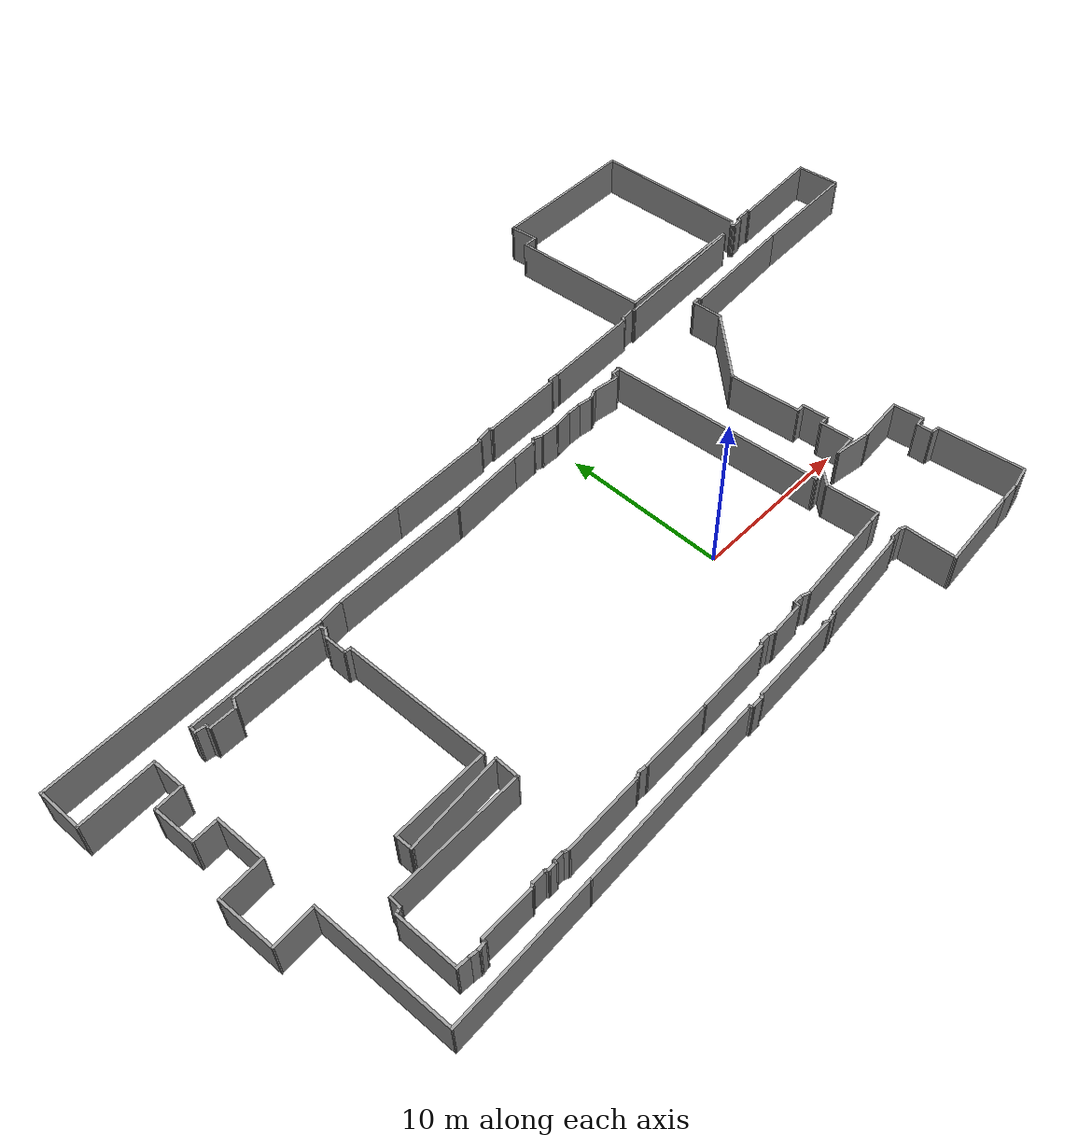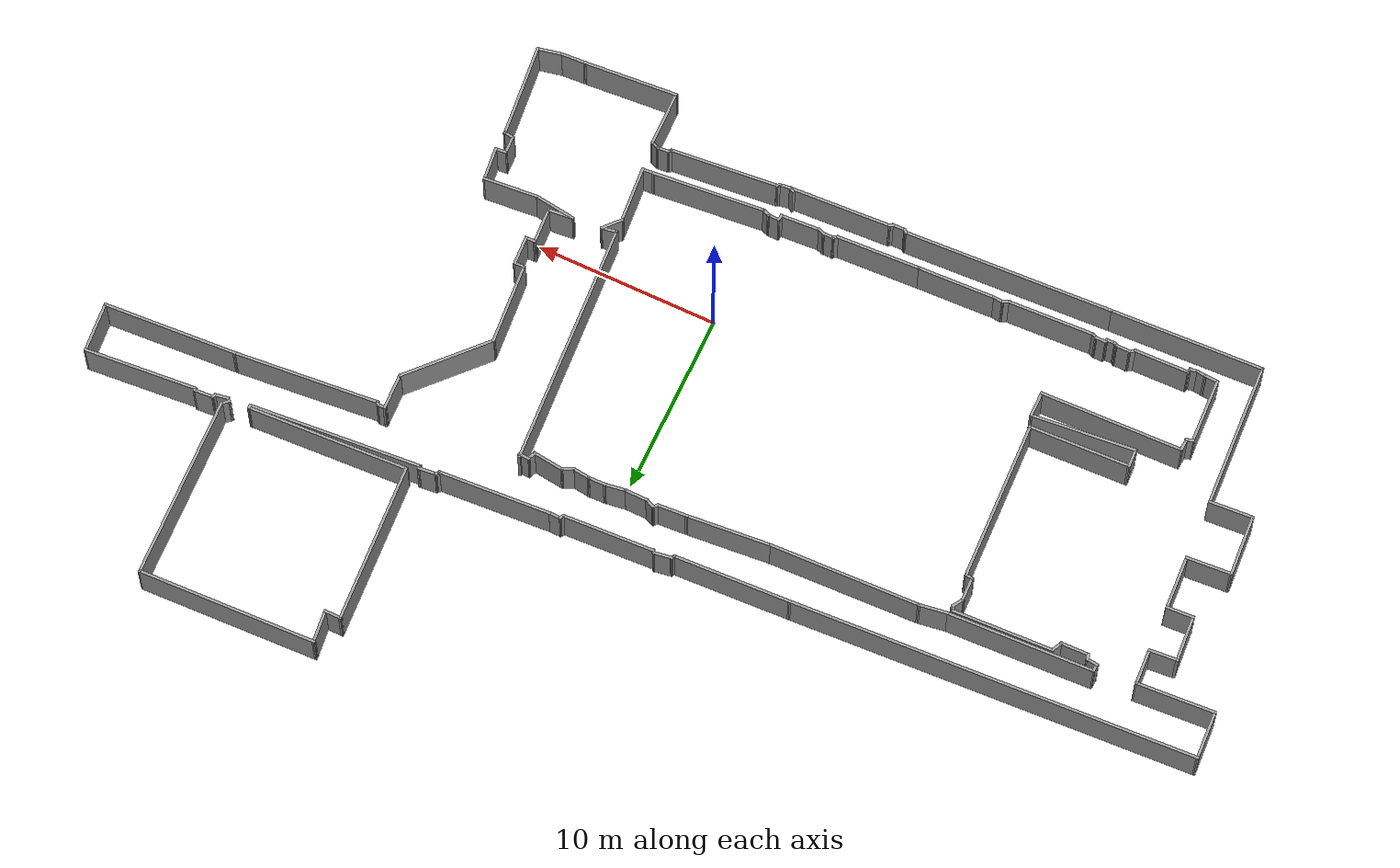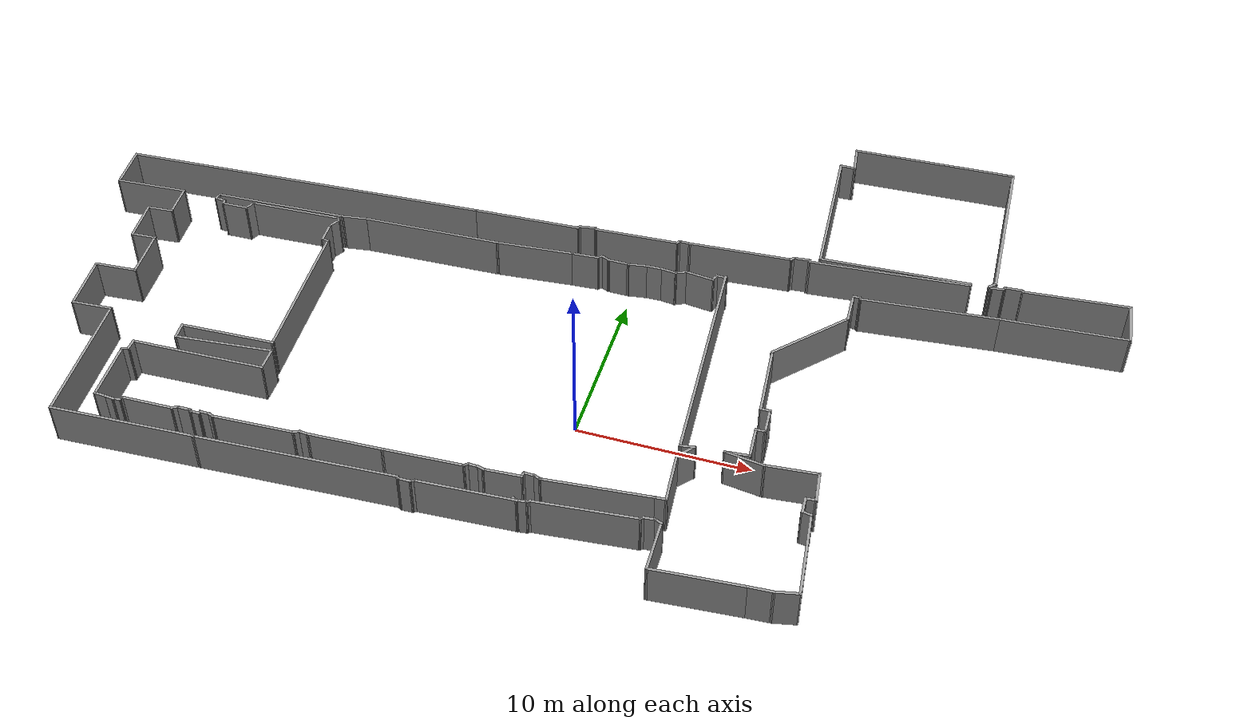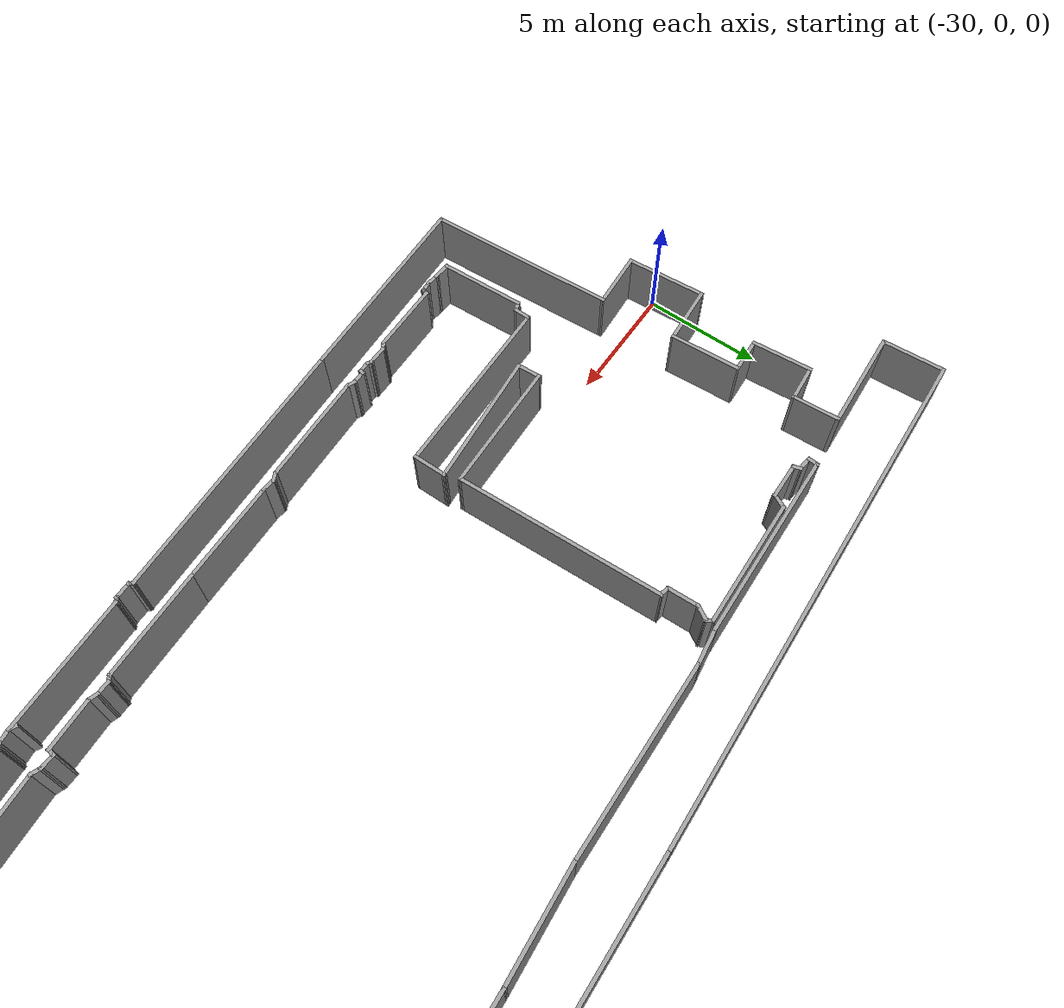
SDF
<?xml version='1.0'?>
<sdf version='1.7'>
  <model name='EnvDC06'>
    <pose>-1.99771 7.86282 0 0 -0 0</pose>
    <link name='Wall_0'>
      <collision name='Wall_0_Collision'>
        <geometry>
          <box>
            <size>1 0.15 2.5</size>
          </box>
        </geometry>
        <pose>0 0 1.25 0 -0 0</pose>
      </collision>
      <visual name='Wall_0_Visual'>
        <pose>0 0 1.25 0 -0 0</pose>
        <geometry>
          <box>
            <size>1 0.15 2.5</size>
          </box>
        </geometry>
        <material>
          <script>
            <uri>file://media/materials/scripts/gazebo.material</uri>
            <name>Gazebo/Grey</name>
          </script>
          <ambient>1 1 1 1</ambient>
        </material>
        <meta>
          <layer>0</layer>
        </meta>
      </visual>
      <pose>12.1528 15.725 0 0 -0 0</pose>
    </link>
    <link name='Wall_1'>
      <collision name='Wall_1_Collision'>
        <geometry>
          <box>
            <size>1.87529 0.15 2.5</size>
          </box>
        </geometry>
        <pose>0 0 1.25 0 -0 0</pose>
      </collision>
      <visual name='Wall_1_Visual'>
        <pose>0 0 1.25 0 -0 0</pose>
        <geometry>
          <box>
            <size>1.87529 0.15 2.5</size>
          </box>
        </geometry>
        <material>
          <script>
            <uri>file://media/materials/scripts/gazebo.material</uri>
            <name>Gazebo/Grey</name>
          </script>
          <ambient>1 1 1 1</ambient>
        </material>
        <meta>
          <layer>0</layer>
        </meta>
      </visual>
      <pose>12.4735 16.5813 0 0 -0 1.69199</pose>
    </link>
    <link name='Wall_10'>
      <collision name='Wall_10_Collision'>
        <geometry>
          <box>
            <size>0.255426 0.15 2.5</size>
          </box>
        </geometry>
        <pose>0 0 1.25 0 -0 0</pose>
      </collision>
      <visual name='Wall_10_Visual'>
        <pose>0 0 1.25 0 -0 0</pose>
        <geometry>
          <box>
            <size>0.255426 0.15 2.5</size>
          </box>
        </geometry>
        <material>
          <script>
            <uri>file://media/materials/scripts/gazebo.material</uri>
            <name>Gazebo/Grey</name>
          </script>
          <ambient>1 1 1 1</ambient>
        </material>
        <meta>
          <layer>0</layer>
        </meta>
      </visual>
      <pose>24.0145 7.75655 0 0 -0 -1.35213</pose>
    </link>
    <link name='Wall_100'>
      <collision name='Wall_100_Collision'>
        <geometry>
          <box>
            <size>0.755861 0.15 2.5</size>
          </box>
        </geometry>
        <pose>0 0 1.25 0 -0 0</pose>
      </collision>
      <visual name='Wall_100_Visual'>
        <pose>0 0 1.25 0 -0 0</pose>
        <geometry>
          <box>
            <size>0.755861 0.15 2.5</size>
          </box>
        </geometry>
        <material>
          <script>
            <uri>file://media/materials/scripts/gazebo.material</uri>
            <name>Gazebo/Grey</name>
          </script>
          <ambient>1 1 1 1</ambient>
        </material>
        <meta>
          <layer>0</layer>
        </meta>
      </visual>
      <pose>8.31616 -13.2267 0 0 -0 -3.07717</pose>
    </link>
    <link name='Wall_101'>
      <collision name='Wall_101_Collision'>
        <geometry>
          <box>
            <size>6.22065 0.15 2.5</size>
          </box>
        </geometry>
        <pose>0 0 1.25 0 -0 0</pose>
      </collision>
      <visual name='Wall_101_Visual'>
        <pose>0 0 1.25 0 -0 0</pose>
        <geometry>
          <box>
            <size>6.22065 0.15 2.5</size>
          </box>
        </geometry>
        <material>
          <script>
            <uri>file://media/materials/scripts/gazebo.material</uri>
            <name>Gazebo/Grey</name>
          </script>
          <ambient>1 1 1 1</ambient>
        </material>
        <meta>
          <layer>0</layer>
        </meta>
      </visual>
      <pose>4.99084 -13.5192 0 0 -0 -3.05152</pose>
    </link>
    <link name='Wall_102'>
      <collision name='Wall_102_Collision'>
        <geometry>
          <box>
            <size>0.544913 0.15 2.5</size>
          </box>
        </geometry>
        <pose>0 0 1.25 0 -0 0</pose>
      </collision>
      <visual name='Wall_102_Visual'>
        <pose>0 0 1.25 0 -0 0</pose>
        <geometry>
          <box>
            <size>0.544913 0.15 2.5</size>
          </box>
        </geometry>
        <material>
          <script>
            <uri>file://media/materials/scripts/gazebo.material</uri>
            <name>Gazebo/Grey</name>
          </script>
          <ambient>1 1 1 1</ambient>
        </material>
        <meta>
          <layer>0</layer>
        </meta>
      </visual>
      <pose>1.78254 -13.724 0 0 -0 2.7886</pose>
    </link>
    <link name='Wall_103'>
      <collision name='Wall_103_Collision'>
        <geometry>
          <box>
            <size>0.715933 0.15 2.5</size>
          </box>
        </geometry>
        <pose>0 0 1.25 0 -0 0</pose>
      </collision>
      <visual name='Wall_103_Visual'>
        <pose>0 0 1.25 0 -0 0</pose>
        <geometry>
          <box>
            <size>0.715933 0.15 2.5</size>
          </box>
        </geometry>
        <material>
          <script>
            <uri>file://media/materials/scripts/gazebo.material</uri>
            <name>Gazebo/Grey</name>
          </script>
          <ambient>1 1 1 1</ambient>
        </material>
        <meta>
          <layer>0</layer>
        </meta>
      </visual>
      <pose>1.31446 -13.646 0 0 -0 3.10712</pose>
    </link>
    <link name='Wall_104'>
      <collision name='Wall_104_Collision'>
        <geometry>
          <box>
            <size>0.420217 0.15 2.5</size>
          </box>
        </geometry>
        <pose>0 0 1.25 0 -0 0</pose>
      </collision>
      <visual name='Wall_104_Visual'>
        <pose>0 0 1.25 0 -0 0</pose>
        <geometry>
          <box>
            <size>0.420217 0.15 2.5</size>
          </box>
        </geometry>
        <material>
          <script>
            <uri>file://media/materials/scripts/gazebo.material</uri>
            <name>Gazebo/Grey</name>
          </script>
          <ambient>1 1 1 1</ambient>
        </material>
        <meta>
          <layer>0</layer>
        </meta>
      </visual>
      <pose>1.00864 -13.7694 0 0 -0 -1.74203</pose>
    </link>
    <link name='Wall_105'>
      <collision name='Wall_105_Collision'>
        <geometry>
          <box>
            <size>2.22808 0.15 2.5</size>
          </box>
        </geometry>
        <pose>0 0 1.25 0 -0 0</pose>
      </collision>
      <visual name='Wall_105_Visual'>
        <pose>0 0 1.25 0 -0 0</pose>
        <geometry>
          <box>
            <size>2.22808 0.15 2.5</size>
          </box>
        </geometry>
        <material>
          <script>
            <uri>file://media/materials/scripts/gazebo.material</uri>
            <name>Gazebo/Grey</name>
          </script>
          <ambient>1 1 1 1</ambient>
        </material>
        <meta>
          <layer>0</layer>
        </meta>
      </visual>
      <pose>-0.051496 -13.9658 0 0 -0 -3.08063</pose>
    </link>
    <link name='Wall_11'>
      <collision name='Wall_11_Collision'>
        <geometry>
          <box>
            <size>6.22574 0.15 2.5</size>
          </box>
        </geometry>
        <pose>0 0 1.25 0 -0 0</pose>
      </collision>
      <visual name='Wall_11_Visual'>
        <pose>0 0 1.25 0 -0 0</pose>
        <geometry>
          <box>
            <size>6.22574 0.15 2.5</size>
          </box>
        </geometry>
        <material>
          <script>
            <uri>file://media/materials/scripts/gazebo.material</uri>
            <name>Gazebo/Grey</name>
          </script>
          <ambient>1 1 1 1</ambient>
        </material>
        <meta>
          <layer>0</layer>
        </meta>
      </visual>
      <pose>27.0534 7.95666 0 0 -0 0.082907</pose>
    </link>
    <link name='Wall_111'>
      <collision name='Wall_111_Collision'>
        <geometry>
          <box>
            <size>0.496157 0.15 2.5</size>
          </box>
        </geometry>
        <pose>0 0 1.25 0 -0 0</pose>
      </collision>
      <visual name='Wall_111_Visual'>
        <pose>0 0 1.25 0 -0 0</pose>
        <geometry>
          <box>
            <size>0.496157 0.15 2.5</size>
          </box>
        </geometry>
        <material>
          <script>
            <uri>file://media/materials/scripts/gazebo.material</uri>
            <name>Gazebo/Grey</name>
          </script>
          <ambient>1 1 1 1</ambient>
        </material>
        <meta>
          <layer>0</layer>
        </meta>
      </visual>
      <pose>-1.25341 -13.9763 0 0 -0 2.8312</pose>
    </link>
    <link name='Wall_112'>
      <collision name='Wall_112_Collision'>
        <geometry>
          <box>
            <size>0.682216 0.15 2.5</size>
          </box>
        </geometry>
        <pose>0 0 1.25 0 -0 0</pose>
      </collision>
      <visual name='Wall_112_Visual'>
        <pose>0 0 1.25 0 -0 0</pose>
        <geometry>
          <box>
            <size>0.682216 0.15 2.5</size>
          </box>
        </geometry>
        <material>
          <script>
            <uri>file://media/materials/scripts/gazebo.material</uri>
            <name>Gazebo/Grey</name>
          </script>
          <ambient>1 1 1 1</ambient>
        </material>
        <meta>
          <layer>0</layer>
        </meta>
      </visual>
      <pose>-1.68433 -13.9234 0 0 -0 3.14159</pose>
    </link>
    <link name='Wall_113'>
      <collision name='Wall_113_Collision'>
        <geometry>
          <box>
            <size>0.403477 0.15 2.5</size>
          </box>
        </geometry>
        <pose>0 0 1.25 0 -0 0</pose>
      </collision>
      <visual name='Wall_113_Visual'>
        <pose>0 0 1.25 0 -0 0</pose>
        <geometry>
          <box>
            <size>0.403477 0.15 2.5</size>
          </box>
        </geometry>
        <material>
          <script>
            <uri>file://media/materials/scripts/gazebo.material</uri>
            <name>Gazebo/Grey</name>
          </script>
          <ambient>1 1 1 1</ambient>
        </material>
        <meta>
          <layer>0</layer>
        </meta>
      </visual>
      <pose>-2.05615 -13.9933 0 0 -0 -2.55732</pose>
    </link>
    <link name='Wall_114'>
      <collision name='Wall_114_Collision'>
        <geometry>
          <box>
            <size>4.64567 0.15 2.5</size>
          </box>
        </geometry>
        <pose>0 0 1.25 0 -0 0</pose>
      </collision>
      <visual name='Wall_114_Visual'>
        <pose>0 0 1.25 0 -0 0</pose>
        <geometry>
          <box>
            <size>4.64567 0.15 2.5</size>
          </box>
        </geometry>
        <material>
          <script>
            <uri>file://media/materials/scripts/gazebo.material</uri>
            <name>Gazebo/Grey</name>
          </script>
          <ambient>1 1 1 1</ambient>
        </material>
        <meta>
          <layer>0</layer>
        </meta>
      </visual>
      <pose>-4.40738 -14.1701 0 0 -0 -3.09617</pose>
    </link>
    <link name='Wall_116'>
      <collision name='Wall_116_Collision'>
        <geometry>
          <box>
            <size>4.34413 0.15 2.5</size>
          </box>
        </geometry>
        <pose>0 0 1.25 0 -0 0</pose>
      </collision>
      <visual name='Wall_116_Visual'>
        <pose>0 0 1.25 0 -0 0</pose>
        <geometry>
          <box>
            <size>4.34413 0.15 2.5</size>
          </box>
        </geometry>
        <material>
          <script>
            <uri>file://media/materials/scripts/gazebo.material</uri>
            <name>Gazebo/Grey</name>
          </script>
          <ambient>1 1 1 1</ambient>
        </material>
        <meta>
          <layer>0</layer>
        </meta>
      </visual>
      <pose>-8.74854 -14.3495 0 0 -0 -3.10472</pose>
    </link>
    <link name='Wall_117'>
      <collision name='Wall_117_Collision'>
        <geometry>
          <box>
            <size>0.657664 0.15 2.5</size>
          </box>
        </geometry>
        <pose>0 0 1.25 0 -0 0</pose>
      </collision>
      <visual name='Wall_117_Visual'>
        <pose>0 0 1.25 0 -0 0</pose>
        <geometry>
          <box>
            <size>0.657664 0.15 2.5</size>
          </box>
        </geometry>
        <material>
          <script>
            <uri>file://media/materials/scripts/gazebo.material</uri>
            <name>Gazebo/Grey</name>
          </script>
          <ambient>1 1 1 1</ambient>
        </material>
        <meta>
          <layer>0</layer>
        </meta>
      </visual>
      <pose>-11.0971 -14.4057 0 0 -0 3.05845</pose>
    </link>
    <link name='Wall_118'>
      <collision name='Wall_118_Collision'>
        <geometry>
          <box>
            <size>0.478084 0.15 2.5</size>
          </box>
        </geometry>
        <pose>0 0 1.25 0 -0 0</pose>
      </collision>
      <visual name='Wall_118_Visual'>
        <pose>0 0 1.25 0 -0 0</pose>
        <geometry>
          <box>
            <size>0.478084 0.15 2.5</size>
          </box>
        </geometry>
        <material>
          <script>
            <uri>file://media/materials/scripts/gazebo.material</uri>
            <name>Gazebo/Grey</name>
          </script>
          <ambient>1 1 1 1</ambient>
        </material>
        <meta>
          <layer>0</layer>
        </meta>
      </visual>
      <pose>-11.4976 -14.4563 0 0 -0 -2.68944</pose>
    </link>
    <link name='Wall_119'>
      <collision name='Wall_119_Collision'>
        <geometry>
          <box>
            <size>4.75823 0.15 2.5</size>
          </box>
        </geometry>
        <pose>0 0 1.25 0 -0 0</pose>
      </collision>
      <visual name='Wall_119_Visual'>
        <pose>0 0 1.25 0 -0 0</pose>
        <geometry>
          <box>
            <size>4.75823 0.15 2.5</size>
          </box>
        </geometry>
        <material>
          <script>
            <uri>file://media/materials/scripts/gazebo.material</uri>
            <name>Gazebo/Grey</name>
          </script>
          <ambient>1 1 1 1</ambient>
        </material>
        <meta>
          <layer>0</layer>
        </meta>
      </visual>
      <pose>-13.9471 -14.6292 0 0 -0 -3.09767</pose>
    </link>
    <link name='Wall_12'>
      <collision name='Wall_12_Collision'>
        <geometry>
          <box>
            <size>2.83708 0.15 2.5</size>
          </box>
        </geometry>
        <pose>0 0 1.25 0 -0 0</pose>
      </collision>
      <visual name='Wall_12_Visual'>
        <pose>0 0 1.25 0 -0 0</pose>
        <geometry>
          <box>
            <size>2.83708 0.15 2.5</size>
          </box>
        </geometry>
        <material>
          <script>
            <uri>file://media/materials/scripts/gazebo.material</uri>
            <name>Gazebo/Grey</name>
          </script>
          <ambient>1 1 1 1</ambient>
        </material>
        <meta>
          <layer>0</layer>
        </meta>
      </visual>
      <pose>30.2037 6.87033 0 0 -0 -1.47917</pose>
    </link>
    <link name='Wall_121'>
      <collision name='Wall_121_Collision'>
        <geometry>
          <box>
            <size>0.441234 0.15 2.5</size>
          </box>
        </geometry>
        <pose>0 0 1.25 0 -0 0</pose>
      </collision>
      <visual name='Wall_121_Visual'>
        <pose>0 0 1.25 0 -0 0</pose>
        <geometry>
          <box>
            <size>0.441234 0.15 2.5</size>
          </box>
        </geometry>
        <material>
          <script>
            <uri>file://media/materials/scripts/gazebo.material</uri>
            <name>Gazebo/Grey</name>
          </script>
          <ambient>1 1 1 1</ambient>
        </material>
        <meta>
          <layer>0</layer>
        </meta>
      </visual>
      <pose>-16.3839 -14.6755 0 0 -0 2.75571</pose>
    </link>
    <link name='Wall_122'>
      <collision name='Wall_122_Collision'>
        <geometry>
          <box>
            <size>0.664342 0.15 2.5</size>
          </box>
        </geometry>
        <pose>0 0 1.25 0 -0 0</pose>
      </collision>
      <visual name='Wall_122_Visual'>
        <pose>0 0 1.25 0 -0 0</pose>
        <geometry>
          <box>
            <size>0.664342 0.15 2.5</size>
          </box>
        </geometry>
        <material>
          <script>
            <uri>file://media/materials/scripts/gazebo.material</uri>
            <name>Gazebo/Grey</name>
          </script>
          <ambient>1 1 1 1</ambient>
        </material>
        <meta>
          <layer>0</layer>
        </meta>
      </visual>
      <pose>-16.776 -14.6207 0 0 -0 3.14159</pose>
    </link>
    <link name='Wall_123'>
      <collision name='Wall_123_Collision'>
        <geometry>
          <box>
            <size>0.272769 0.15 2.5</size>
          </box>
        </geometry>
        <pose>0 0 1.25 0 -0 0</pose>
      </collision>
      <visual name='Wall_123_Visual'>
        <pose>0 0 1.25 0 -0 0</pose>
        <geometry>
          <box>
            <size>0.272769 0.15 2.5</size>
          </box>
        </geometry>
        <material>
          <script>
            <uri>file://media/materials/scripts/gazebo.material</uri>
            <name>Gazebo/Grey</name>
          </script>
          <ambient>1 1 1 1</ambient>
        </material>
        <meta>
          <layer>0</layer>
        </meta>
      </visual>
      <pose>-17.05 -14.6798 0 0 -0 -1.8491</pose>
    </link>
    <link name='Wall_124'>
      <collision name='Wall_124_Collision'>
        <geometry>
          <box>
            <size>0.58878 0.15 2.5</size>
          </box>
        </geometry>
        <pose>0 0 1.25 0 -0 0</pose>
      </collision>
      <visual name='Wall_124_Visual'>
        <pose>0 0 1.25 0 -0 0</pose>
        <geometry>
          <box>
            <size>0.58878 0.15 2.5</size>
          </box>
        </geometry>
        <material>
          <script>
            <uri>file://media/materials/scripts/gazebo.material</uri>
            <name>Gazebo/Grey</name>
          </script>
          <ambient>1 1 1 1</ambient>
        </material>
        <meta>
          <layer>0</layer>
        </meta>
      </visual>
      <pose>-17.2861 -14.743 0 0 -0 -3.12236</pose>
    </link>
    <link name='Wall_125'>
      <collision name='Wall_125_Collision'>
        <geometry>
          <box>
            <size>0.309092 0.15 2.5</size>
          </box>
        </geometry>
        <pose>0 0 1.25 0 -0 0</pose>
      </collision>
      <visual name='Wall_125_Visual'>
        <pose>0 0 1.25 0 -0 0</pose>
        <geometry>
          <box>
            <size>0.309092 0.15 2.5</size>
          </box>
        </geometry>
        <material>
          <script>
            <uri>file://media/materials/scripts/gazebo.material</uri>
            <name>Gazebo/Grey</name>
          </script>
          <ambient>1 1 1 1</ambient>
        </material>
        <meta>
          <layer>0</layer>
        </meta>
      </visual>
      <pose>-17.5728 -14.7051 0 0 -0 2.58299</pose>
    </link>
    <link name='Wall_126'>
      <collision name='Wall_126_Collision'>
        <geometry>
          <box>
            <size>0.875138 0.15 2.5</size>
          </box>
        </geometry>
        <pose>0 0 1.25 0 -0 0</pose>
      </collision>
      <visual name='Wall_126_Visual'>
        <pose>0 0 1.25 0 -0 0</pose>
        <geometry>
          <box>
            <size>0.875138 0.15 2.5</size>
          </box>
        </geometry>
        <material>
          <script>
            <uri>file://media/materials/scripts/gazebo.material</uri>
            <name>Gazebo/Grey</name>
          </script>
          <ambient>1 1 1 1</ambient>
        </material>
        <meta>
          <layer>0</layer>
        </meta>
      </visual>
      <pose>-18.0028 -14.6629 0 0 -0 3.14159</pose>
    </link>
    <link name='Wall_127'>
      <collision name='Wall_127_Collision'>
        <geometry>
          <box>
            <size>0.449419 0.15 2.5</size>
          </box>
        </geometry>
        <pose>0 0 1.25 0 -0 0</pose>
      </collision>
      <visual name='Wall_127_Visual'>
        <pose>0 0 1.25 0 -0 0</pose>
        <geometry>
          <box>
            <size>0.449419 0.15 2.5</size>
          </box>
        </geometry>
        <material>
          <script>
            <uri>file://media/materials/scripts/gazebo.material</uri>
            <name>Gazebo/Grey</name>
          </script>
          <ambient>1 1 1 1</ambient>
        </material>
        <meta>
          <layer>0</layer>
        </meta>
      </visual>
      <pose>-18.4919 -14.743 0 0 -0 -2.57702</pose>
    </link>
    <link name='Wall_128'>
      <collision name='Wall_128_Collision'>
        <geometry>
          <box>
            <size>3.06046 0.15 2.5</size>
          </box>
        </geometry>
        <pose>0 0 1.25 0 -0 0</pose>
      </collision>
      <visual name='Wall_128_Visual'>
        <pose>0 0 1.25 0 -0 0</pose>
        <geometry>
          <box>
            <size>3.06046 0.15 2.5</size>
          </box>
        </geometry>
        <material>
          <script>
            <uri>file://media/materials/scripts/gazebo.material</uri>
            <name>Gazebo/Grey</name>
          </script>
          <ambient>1 1 1 1</ambient>
        </material>
        <meta>
          <layer>0</layer>
        </meta>
      </visual>
      <pose>-20.0728 -14.8568 0 0 -0 -3.11841</pose>
    </link>
    <link name='Wall_129'>
      <collision name='Wall_129_Collision'>
        <geometry>
          <box>
            <size>0.342276 0.15 2.5</size>
          </box>
        </geometry>
        <pose>0 0 1.25 0 -0 0</pose>
      </collision>
      <visual name='Wall_129_Visual'>
        <pose>0 0 1.25 0 -0 0</pose>
        <geometry>
          <box>
            <size>0.342276 0.15 2.5</size>
          </box>
        </geometry>
        <material>
          <script>
            <uri>file://media/materials/scripts/gazebo.material</uri>
            <name>Gazebo/Grey</name>
          </script>
          <ambient>1 1 1 1</ambient>
        </material>
        <meta>
          <layer>0</layer>
        </meta>
      </visual>
      <pose>-21.5526 -14.9833 0 0 -0 -1.83705</pose>
    </link>
    <link name='Wall_130'>
      <collision name='Wall_130_Collision'>
        <geometry>
          <box>
            <size>0.532791 0.15 2.5</size>
          </box>
        </geometry>
        <pose>0 0 1.25 0 -0 0</pose>
      </collision>
      <visual name='Wall_130_Visual'>
        <pose>0 0 1.25 0 -0 0</pose>
        <geometry>
          <box>
            <size>0.532791 0.15 2.5</size>
          </box>
        </geometry>
        <material>
          <script>
            <uri>file://media/materials/scripts/gazebo.material</uri>
            <name>Gazebo/Grey</name>
          </script>
          <ambient>1 1 1 1</ambient>
        </material>
        <meta>
          <layer>0</layer>
        </meta>
      </visual>
      <pose>-21.7676 -15.1014 0 0 -0 -3.00904</pose>
    </link>
    <link name='Wall_131'>
      <collision name='Wall_131_Collision'>
        <geometry>
          <box>
            <size>0.634225 0.15 2.5</size>
          </box>
        </geometry>
        <pose>0 0 1.25 0 -0 0</pose>
      </collision>
      <visual name='Wall_131_Visual'>
        <pose>0 0 1.25 0 -0 0</pose>
        <geometry>
          <box>
            <size>0.634225 0.15 2.5</size>
          </box>
        </geometry>
        <material>
          <script>
            <uri>file://media/materials/scripts/gazebo.material</uri>
            <name>Gazebo/Grey</name>
          </script>
          <ambient>1 1 1 1</ambient>
        </material>
        <meta>
          <layer>0</layer>
        </meta>
      </visual>
      <pose>-22.1977 -15.1014 0 0 -0 3.03672</pose>
    </link>
    <link name='Wall_132'>
      <collision name='Wall_132_Collision'>
        <geometry>
          <box>
            <size>0.817448 0.15 2.5</size>
          </box>
        </geometry>
        <pose>0 0 1.25 0 -0 0</pose>
      </collision>
      <visual name='Wall_132_Visual'>
        <pose>0 0 1.25 0 -0 0</pose>
        <geometry>
          <box>
            <size>0.817448 0.15 2.5</size>
          </box>
        </geometry>
        <material>
          <script>
            <uri>file://media/materials/scripts/gazebo.material</uri>
            <name>Gazebo/Grey</name>
          </script>
          <ambient>1 1 1 1</ambient>
        </material>
        <meta>
          <layer>0</layer>
        </meta>
      </visual>
      <pose>-22.771 -15.055 0 0 -0 3.07839</pose>
    </link>
    <link name='Wall_133'>
      <collision name='Wall_133_Collision'>
        <geometry>
          <box>
            <size>3.62843 0.15 2.5</size>
          </box>
        </geometry>
        <pose>0 0 1.25 0 -0 0</pose>
      </collision>
      <visual name='Wall_133_Visual'>
        <pose>0 0 1.25 0 -0 0</pose>
        <geometry>
          <box>
            <size>3.62843 0.15 2.5</size>
          </box>
        </geometry>
        <material>
          <script>
            <uri>file://media/materials/scripts/gazebo.material</uri>
            <name>Gazebo/Grey</name>
          </script>
          <ambient>1 1 1 1</ambient>
        </material>
        <meta>
          <layer>0</layer>
        </meta>
      </visual>
      <pose>-23.1926 -13.2969 0 0 -0 1.62172</pose>
    </link>
    <link name='Wall_138'>
      <collision name='Wall_138_Collision'>
        <geometry>
          <box>
            <size>0.501012 0.15 2.5</size>
          </box>
        </geometry>
        <pose>0 0 1.25 0 -0 0</pose>
      </collision>
      <visual name='Wall_138_Visual'>
        <pose>0 0 1.25 0 -0 0</pose>
        <geometry>
          <box>
            <size>0.501012 0.15 2.5</size>
          </box>
        </geometry>
        <material>
          <script>
            <uri>file://media/materials/scripts/gazebo.material</uri>
            <name>Gazebo/Grey</name>
          </script>
          <ambient>1 1 1 1</ambient>
        </material>
        <meta>
          <layer>0</layer>
        </meta>
      </visual>
      <pose>-23.1209 -11.4883 0 0 -0 0.420663</pose>
    </link>
    <link name='Wall_139'>
      <collision name='Wall_139_Collision'>
        <geometry>
          <box>
            <size>0.748898 0.15 2.5</size>
          </box>
        </geometry>
        <pose>0 0 1.25 0 -0 0</pose>
      </collision>
      <visual name='Wall_139_Visual'>
        <pose>0 0 1.25 0 -0 0</pose>
        <geometry>
          <box>
            <size>0.748898 0.15 2.5</size>
          </box>
        </geometry>
        <material>
          <script>
            <uri>file://media/materials/scripts/gazebo.material</uri>
            <name>Gazebo/Grey</name>
          </script>
          <ambient>1 1 1 1</ambient>
        </material>
        <meta>
          <layer>0</layer>
        </meta>
      </visual>
      <pose>-22.9523 -11.1173 0 0 -0 1.54263</pose>
    </link>
    <link name='Wall_14'>
      <collision name='Wall_14_Collision'>
        <geometry>
          <box>
            <size>7.39108 0.15 2.5</size>
          </box>
        </geometry>
        <pose>0 0 1.25 0 -0 0</pose>
      </collision>
      <visual name='Wall_14_Visual'>
        <pose>0 0 1.25 0 -0 0</pose>
        <geometry>
          <box>
            <size>7.39108 0.15 2.5</size>
          </box>
        </geometry>
        <material>
          <script>
            <uri>file://media/materials/scripts/gazebo.material</uri>
            <name>Gazebo/Grey</name>
          </script>
          <ambient>1 1 1 1</ambient>
        </material>
        <meta>
          <layer>0</layer>
        </meta>
      </visual>
      <pose>26.713 5.30981 0 0 -0 -3.08007</pose>
    </link>
    <link name='Wall_140'>
      <collision name='Wall_140_Collision'>
        <geometry>
          <box>
            <size>7.85115 0.15 2.5</size>
          </box>
        </geometry>
        <pose>0 0 1.25 0 -0 0</pose>
      </collision>
      <visual name='Wall_140_Visual'>
        <pose>0 0 1.25 0 -0 0</pose>
        <geometry>
          <box>
            <size>7.85115 0.15 2.5</size>
          </box>
        </geometry>
        <material>
          <script>
            <uri>file://media/materials/scripts/gazebo.material</uri>
            <name>Gazebo/Grey</name>
          </script>
          <ambient>1 1 1 1</ambient>
        </material>
        <meta>
          <layer>0</layer>
        </meta>
      </visual>
      <pose>-19.0947 -10.7126 0 0 -0 0.027375</pose>
    </link>
    <link name='Wall_141'>
      <collision name='Wall_141_Collision'>
        <geometry>
          <box>
            <size>1.49069 0.15 2.5</size>
          </box>
        </geometry>
        <pose>0 0 1.25 0 -0 0</pose>
      </collision>
      <visual name='Wall_141_Visual'>
        <pose>0 0 1.25 0 -0 0</pose>
        <geometry>
          <box>
            <size>1.49069 0.15 2.5</size>
          </box>
        </geometry>
        <material>
          <script>
            <uri>file://media/materials/scripts/gazebo.material</uri>
            <name>Gazebo/Grey</name>
          </script>
          <ambient>1 1 1 1</ambient>
        </material>
        <meta>
          <layer>0</layer>
        </meta>
      </visual>
      <pose>-15.2498 -9.93685 0 0 -0 1.57709</pose>
    </link>
    <link name='Wall_142'>
      <collision name='Wall_142_Collision'>
        <geometry>
          <box>
            <size>5.7647 0.15 2.5</size>
          </box>
        </geometry>
        <pose>0 0 1.25 0 -0 0</pose>
      </collision>
      <visual name='Wall_142_Visual'>
        <pose>0 0 1.25 0 -0 0</pose>
        <geometry>
          <box>
            <size>5.7647 0.15 2.5</size>
          </box>
        </geometry>
        <material>
          <script>
            <uri>file://media/materials/scripts/gazebo.material</uri>
            <name>Gazebo/Grey</name>
          </script>
          <ambient>1 1 1 1</ambient>
        </material>
        <meta>
          <layer>0</layer>
        </meta>
      </visual>
      <pose>-18.0492 -9.52791 0 0 -0 -3.04835</pose>
    </link>
    <link name='Wall_143'>
      <collision name='Wall_143_Collision'>
        <geometry>
          <box>
            <size>1.07995 0.15 2.5</size>
          </box>
        </geometry>
        <pose>0 0 1.25 0 -0 0</pose>
      </collision>
      <visual name='Wall_143_Visual'>
        <pose>0 0 1.25 0 -0 0</pose>
        <geometry>
          <box>
            <size>1.07995 0.15 2.5</size>
          </box>
        </geometry>
        <material>
          <script>
            <uri>file://media/materials/scripts/gazebo.material</uri>
            <name>Gazebo/Grey</name>
          </script>
          <ambient>1 1 1 1</ambient>
        </material>
        <meta>
          <layer>0</layer>
        </meta>
      </visual>
      <pose>-20.8739 -9.32554 0 0 -0 1.63435</pose>
    </link>
    <link name='Wall_144'>
      <collision name='Wall_144_Collision'>
        <geometry>
          <box>
            <size>5.5923 0.15 2.5</size>
          </box>
        </geometry>
        <pose>0 0 1.25 0 -0 0</pose>
      </collision>
      <visual name='Wall_144_Visual'>
        <pose>0 0 1.25 0 -0 0</pose>
        <geometry>
          <box>
            <size>5.5923 0.15 2.5</size>
          </box>
        </geometry>
        <material>
          <script>
            <uri>file://media/materials/scripts/gazebo.material</uri>
            <name>Gazebo/Grey</name>
          </script>
          <ambient>1 1 1 1</ambient>
        </material>
        <meta>
          <layer>0</layer>
        </meta>
      </visual>
      <pose>-18.1841 -8.76061 0 0 -0 0.037192</pose>
    </link>
    <link name='Wall_146'>
      <collision name='Wall_146_Collision'>
        <geometry>
          <box>
            <size>8.90349 0.15 2.5</size>
          </box>
        </geometry>
        <pose>0 0 1.25 0 -0 0</pose>
      </collision>
      <visual name='Wall_146_Visual'>
        <pose>0 0 1.25 0 -0 0</pose>
        <geometry>
          <box>
            <size>8.90349 0.15 2.5</size>
          </box>
        </geometry>
        <material>
          <script>
            <uri>file://media/materials/scripts/gazebo.material</uri>
            <name>Gazebo/Grey</name>
          </script>
          <ambient>1 1 1 1</ambient>
        </material>
        <meta>
          <layer>0</layer>
        </meta>
      </visual>
      <pose>-15.6523 -4.2867 0 0 -0 1.61364</pose>
    </link>
    <link name='Wall_147'>
      <collision name='Wall_147_Collision'>
        <geometry>
          <box>
            <size>0.505025 0.15 2.5</size>
          </box>
        </geometry>
        <pose>0 0 1.25 0 -0 0</pose>
      </collision>
      <visual name='Wall_147_Visual'>
        <pose>0 0 1.25 0 -0 0</pose>
        <geometry>
          <box>
            <size>0.505025 0.15 2.5</size>
          </box>
        </geometry>
        <material>
          <script>
            <uri>file://media/materials/scripts/gazebo.material</uri>
            <name>Gazebo/Grey</name>
          </script>
          <ambient>1 1 1 1</ambient>
        </material>
        <meta>
          <layer>0</layer>
        </meta>
      </visual>
      <pose>-16.015 0.114301 0 0 -0 2.98168</pose>
    </link>
    <link name='Wall_148'>
      <collision name='Wall_148_Collision'>
        <geometry>
          <box>
            <size>1.40581 0.15 2.5</size>
          </box>
        </geometry>
        <pose>0 0 1.25 0 -0 0</pose>
      </collision>
      <visual name='Wall_148_Visual'>
        <pose>0 0 1.25 0 -0 0</pose>
        <geometry>
          <box>
            <size>1.40581 0.15 2.5</size>
          </box>
        </geometry>
        <material>
          <script>
            <uri>file://media/materials/scripts/gazebo.material</uri>
            <name>Gazebo/Grey</name>
          </script>
          <ambient>1 1 1 1</ambient>
        </material>
        <meta>
          <layer>0</layer>
        </meta>
      </visual>
      <pose>-16.2128 0.770066 0 0 -0 1.60682</pose>
    </link>
    <link name='Wall_149'>
      <collision name='Wall_149_Collision'>
        <geometry>
          <box>
            <size>0.753061 0.15 2.5</size>
          </box>
        </geometry>
        <pose>0 0 1.25 0 -0 0</pose>
      </collision>
      <visual name='Wall_149_Visual'>
        <pose>0 0 1.25 0 -0 0</pose>
        <geometry>
          <box>
            <size>0.753061 0.15 2.5</size>
          </box>
        </geometry>
        <material>
          <script>
            <uri>file://media/materials/scripts/gazebo.material</uri>
            <name>Gazebo/Grey</name>
          </script>
          <ambient>1 1 1 1</ambient>
        </material>
        <meta>
          <layer>0</layer>
        </meta>
      </visual>
      <pose>-16.0828 1.65761 0 0 -0 1.04002</pose>
    </link>
    <link name='Wall_150'>
      <collision name='Wall_150_Collision'>
        <geometry>
          <box>
            <size>0.402816 0.15 2.5</size>
          </box>
        </geometry>
        <pose>0 0 1.25 0 -0 0</pose>
      </collision>
      <visual name='Wall_150_Visual'>
        <pose>0 0 1.25 0 -0 0</pose>
        <geometry>
          <box>
            <size>0.402816 0.15 2.5</size>
          </box>
        </geometry>
        <material>
          <script>
            <uri>file://media/materials/scripts/gazebo.material</uri>
            <name>Gazebo/Grey</name>
          </script>
          <ambient>1 1 1 1</ambient>
        </material>
        <meta>
          <layer>0</layer>
        </meta>
      </visual>
      <pose>-15.9867 2.03072 0 0 -0 2.03444</pose>
    </link>
    <link name='Wall_151'>
      <collision name='Wall_151_Collision'>
        <geometry>
          <box>
            <size>5.54784 0.15 2.5</size>
          </box>
        </geometry>
        <pose>0 0 1.25 0 -0 0</pose>
      </collision>
      <visual name='Wall_151_Visual'>
        <pose>0 0 1.25 0 -0 0</pose>
        <geometry>
          <box>
            <size>5.54784 0.15 2.5</size>
          </box>
        </geometry>
        <material>
          <script>
            <uri>file://media/materials/scripts/gazebo.material</uri>
            <name>Gazebo/Grey</name>
          </script>
          <ambient>1 1 1 1</ambient>
        </material>
        <meta>
          <layer>0</layer>
        </meta>
      </visual>
      <pose>-18.7398 2.03072 0 0 -0 -3.09969</pose>
    </link>
    <link name='Wall_152'>
      <collision name='Wall_152_Collision'>
        <geometry>
          <box>
            <size>0.731478 0.15 2.5</size>
          </box>
        </geometry>
        <pose>0 0 1.25 0 -0 0</pose>
      </collision>
      <visual name='Wall_152_Visual'>
        <pose>0 0 1.25 0 -0 0</pose>
        <geometry>
          <box>
            <size>0.731478 0.15 2.5</size>
          </box>
        </geometry>
        <material>
          <script>
            <uri>file://media/materials/scripts/gazebo.material</uri>
            <name>Gazebo/Grey</name>
          </script>
          <ambient>1 1 1 1</ambient>
        </material>
        <meta>
          <layer>0</layer>
        </meta>
      </visual>
      <pose>-21.5664 1.65761 0 0 -0 -2.03444</pose>
    </link>
    <link name='Wall_153'>
      <collision name='Wall_153_Collision'>
        <geometry>
          <box>
            <size>1.60869 0.15 2.5</size>
          </box>
        </geometry>
        <pose>0 0 1.25 0 -0 0</pose>
      </collision>
      <visual name='Wall_153_Visual'>
        <pose>0 0 1.25 0 -0 0</pose>
        <geometry>
          <box>
            <size>1.60869 0.15 2.5</size>
          </box>
        </geometry>
        <material>
          <script>
            <uri>file://media/materials/scripts/gazebo.material</uri>
            <name>Gazebo/Grey</name>
          </script>
          <ambient>1 1 1 1</ambient>
        </material>
        <meta>
          <layer>0</layer>
        </meta>
      </visual>
      <pose>-22.4256 1.38061 0 0 -0 -3.11834</pose>
    </link>
    <link name='Wall_154'>
      <collision name='Wall_154_Collision'>
        <geometry>
          <box>
            <size>0.411026 0.15 2.5</size>
          </box>
        </geometry>
        <pose>0 0 1.25 0 -0 0</pose>
      </collision>
      <visual name='Wall_154_Visual'>
        <pose>0 0 1.25 0 -0 0</pose>
        <geometry>
          <box>
            <size>0.411026 0.15 2.5</size>
          </box>
        </geometry>
        <material>
          <script>
            <uri>file://media/materials/scripts/gazebo.material</uri>
            <name>Gazebo/Grey</name>
          </script>
          <ambient>1 1 1 1</ambient>
        </material>
        <meta>
          <layer>0</layer>
        </meta>
      </visual>
      <pose>-23.1945 1.48802 0 0 -0 1.87885</pose>
    </link>
    <link name='Wall_155'>
      <collision name='Wall_155_Collision'>
        <geometry>
          <box>
            <size>0.696925 0.15 2.5</size>
          </box>
        </geometry>
        <pose>0 0 1.25 0 -0 0</pose>
      </collision>
      <visual name='Wall_155_Visual'>
        <pose>0 0 1.25 0 -0 0</pose>
        <geometry>
          <box>
            <size>0.696925 0.15 2.5</size>
          </box>
        </geometry>
        <material>
          <script>
            <uri>file://media/materials/scripts/gazebo.material</uri>
            <name>Gazebo/Grey</name>
          </script>
          <ambient>1 1 1 1</ambient>
        </material>
        <meta>
          <layer>0</layer>
        </meta>
      </visual>
      <pose>-23.5054 1.6463 0 0 -0 3.01724</pose>
    </link>
    <link name='Wall_156'>
      <collision name='Wall_156_Collision'>
        <geometry>
          <box>
            <size>0.512507 0.15 2.5</size>
          </box>
        </geometry>
        <pose>0 0 1.25 0 -0 0</pose>
      </collision>
      <visual name='Wall_156_Visual'>
        <pose>0 0 1.25 0 -0 0</pose>
        <geometry>
          <box>
            <size>0.512507 0.15 2.5</size>
          </box>
        </geometry>
        <material>
          <script>
            <uri>file://media/materials/scripts/gazebo.material</uri>
            <name>Gazebo/Grey</name>
          </script>
          <ambient>1 1 1 1</ambient>
        </material>
        <meta>
          <layer>0</layer>
        </meta>
      </visual>
      <pose>-23.7654 1.86112 0 0 -0 1.50838</pose>
    </link>
    <link name='Wall_157'>
      <collision name='Wall_157_Collision'>
        <geometry>
          <box>
            <size>8.07119 0.15 2.5</size>
          </box>
        </geometry>
        <pose>0 0 1.25 0 -0 0</pose>
      </collision>
      <visual name='Wall_157_Visual'>
        <pose>0 0 1.25 0 -0 0</pose>
        <geometry>
          <box>
            <size>8.07119 0.15 2.5</size>
          </box>
        </geometry>
        <material>
          <script>
            <uri>file://media/materials/scripts/gazebo.material</uri>
            <name>Gazebo/Grey</name>
          </script>
          <ambient>1 1 1 1</ambient>
        </material>
        <meta>
          <layer>0</layer>
        </meta>
      </visual>
      <pose>-19.7969 2.20596 0 0 -0 0.041405</pose>
    </link>
    <link name='Wall_158'>
      <collision name='Wall_158_Collision'>
        <geometry>
          <box>
            <size>1.64662 0.15 2.5</size>
          </box>
        </geometry>
        <pose>0 0 1.25 0 -0 0</pose>
      </collision>
      <visual name='Wall_158_Visual'>
        <pose>0 0 1.25 0 -0 0</pose>
        <geometry>
          <box>
            <size>1.64662 0.15 2.5</size>
          </box>
        </geometry>
        <material>
          <script>
            <uri>file://media/materials/scripts/gazebo.material</uri>
            <name>Gazebo/Grey</name>
          </script>
          <ambient>1 1 1 1</ambient>
        </material>
        <meta>
          <layer>0</layer>
        </meta>
      </visual>
      <pose>-15.0992 2.47732 0 0 -0 0.144034</pose>
    </link>
    <link name='Wall_159'>
      <collision name='Wall_159_Collision'>
        <geometry>
          <box>
            <size>8.29544 0.15 2.5</size>
          </box>
        </geometry>
        <pose>0 0 1.25 0 -0 0</pose>
      </collision>
      <visual name='Wall_159_Visual'>
        <pose>0 0 1.25 0 -0 0</pose>
        <geometry>
          <box>
            <size>8.29544 0.15 2.5</size>
          </box>
        </geometry>
        <material>
          <script>
            <uri>file://media/materials/scripts/gazebo.material</uri>
            <name>Gazebo/Grey</name>
          </script>
          <ambient>1 1 1 1</ambient>
        </material>
        <meta>
          <layer>0</layer>
        </meta>
      </visual>
      <pose>-10.2883 2.72606 0 0 -0 0.034708</pose>
    </link>
    <link name='Wall_16'>
      <collision name='Wall_16_Collision'>
        <geometry>
          <box>
            <size>8.02507 0.15 2.5</size>
          </box>
        </geometry>
        <pose>0 0 1.25 0 -0 0</pose>
      </collision>
      <visual name='Wall_16_Visual'>
        <pose>0 0 1.25 0 -0 0</pose>
        <geometry>
          <box>
            <size>8.02507 0.15 2.5</size>
          </box>
        </geometry>
        <material>
          <script>
            <uri>file://media/materials/scripts/gazebo.material</uri>
            <name>Gazebo/Grey</name>
          </script>
          <ambient>1 1 1 1</ambient>
        </material>
        <meta>
          <layer>0</layer>
        </meta>
      </visual>
      <pose>19.1772 4.73871 0 0 -0 -3.05297</pose>
    </link>
    <link name='Wall_160'>
      <collision name='Wall_160_Collision'>
        <geometry>
          <box>
            <size>4.67756 0.15 2.5</size>
          </box>
        </geometry>
        <pose>0 0 1.25 0 -0 0</pose>
      </collision>
      <visual name='Wall_160_Visual'>
        <pose>0 0 1.25 0 -0 0</pose>
        <geometry>
          <box>
            <size>4.67756 0.15 2.5</size>
          </box>
        </geometry>
        <material>
          <script>
            <uri>file://media/materials/scripts/gazebo.material</uri>
            <name>Gazebo/Grey</name>
          </script>
          <ambient>1 1 1 1</ambient>
        </material>
        <meta>
          <layer>0</layer>
        </meta>
      </visual>
      <pose>-3.96247 3.05959 0 0 -0 0.085008</pose>
    </link>
    <link name='Wall_161'>
      <collision name='Wall_161_Collision'>
        <geometry>
          <box>
            <size>1.72564 0.15 2.5</size>
          </box>
        </geometry>
        <pose>0 0 1.25 0 -0 0</pose>
      </collision>
      <visual name='Wall_161_Visual'>
        <pose>0 0 1.25 0 -0 0</pose>
        <geometry>
          <box>
            <size>1.72564 0.15 2.5</size>
          </box>
        </geometry>
        <material>
          <script>
            <uri>file://media/materials/scripts/gazebo.material</uri>
            <name>Gazebo/Grey</name>
          </script>
          <ambient>1 1 1 1</ambient>
        </material>
        <meta>
          <layer>0</layer>
        </meta>
      </visual>
      <pose>-0.921076 3.30268 0 0 -0 0.064658</pose>
    </link>
    <link name='Wall_162'>
      <collision name='Wall_162_Collision'>
        <geometry>
          <box>
            <size>0.413948 0.15 2.5</size>
          </box>
        </geometry>
        <pose>0 0 1.25 0 -0 0</pose>
      </collision>
      <visual name='Wall_162_Visual'>
        <pose>0 0 1.25 0 -0 0</pose>
        <geometry>
          <box>
            <size>0.413948 0.15 2.5</size>
          </box>
        </geometry>
        <material>
          <script>
            <uri>file://media/materials/scripts/gazebo.material</uri>
            <name>Gazebo/Grey</name>
          </script>
          <ambient>1 1 1 1</ambient>
        </material>
        <meta>
          <layer>0</layer>
        </meta>
      </visual>
      <pose>-0.044838 3.44966 0 0 -0 0.815692</pose>
    </link>
    <link name='Wall_163'>
      <collision name='Wall_163_Collision'>
        <geometry>
          <box>
            <size>0.666637 0.15 2.5</size>
          </box>
        </geometry>
        <pose>0 0 1.25 0 -0 0</pose>
      </collision>
      <visual name='Wall_163_Visual'>
        <pose>0 0 1.25 0 -0 0</pose>
        <geometry>
          <box>
            <size>0.666637 0.15 2.5</size>
          </box>
        </geometry>
        <material>
          <script>
            <uri>file://media/materials/scripts/gazebo.material</uri>
            <name>Gazebo/Grey</name>
          </script>
          <ambient>1 1 1 1</ambient>
        </material>
        <meta>
          <layer>0</layer>
        </meta>
      </visual>
      <pose>0.283044 3.444 0 0 -0 -0.404892</pose>
    </link>
    <link name='Wall_164'>
      <collision name='Wall_164_Collision'>
        <geometry>
          <box>
            <size>1.32591 0.15 2.5</size>
          </box>
        </geometry>
        <pose>0 0 1.25 0 -0 0</pose>
      </collision>
      <visual name='Wall_164_Visual'>
        <pose>0 0 1.25 0 -0 0</pose>
        <geometry>
          <box>
            <size>1.32591 0.15 2.5</size>
          </box>
        </geometry>
        <material>
          <script>
            <uri>file://media/materials/scripts/gazebo.material</uri>
            <name>Gazebo/Grey</name>
          </script>
          <ambient>1 1 1 1</ambient>
        </material>
        <meta>
          <layer>0</layer>
        </meta>
      </visual>
      <pose>1.1084 3.33659 0 0 -0 -0.009615</pose>
    </link>
    <link name='Wall_165'>
      <collision name='Wall_165_Collision'>
        <geometry>
          <box>
            <size>1.25807 0.15 2.5</size>
          </box>
        </geometry>
        <pose>0 0 1.25 0 -0 0</pose>
      </collision>
      <visual name='Wall_165_Visual'>
        <pose>0 0 1.25 0 -0 0</pose>
        <geometry>
          <box>
            <size>1.25807 0.15 2.5</size>
          </box>
        </geometry>
        <material>
          <script>
            <uri>file://media/materials/scripts/gazebo.material</uri>
            <name>Gazebo/Grey</name>
          </script>
          <ambient>1 1 1 1</ambient>
        </material>
        <meta>
          <layer>0</layer>
        </meta>
      </visual>
      <pose>2.24469 3.41009 0 0 -0 0.14334</pose>
    </link>
    <link name='Wall_166'>
      <collision name='Wall_166_Collision'>
        <geometry>
          <box>
            <size>1.04384 0.15 2.5</size>
          </box>
        </geometry>
        <pose>0 0 1.25 0 -0 0</pose>
      </collision>
      <visual name='Wall_166_Visual'>
        <pose>0 0 1.25 0 -0 0</pose>
        <geometry>
          <box>
            <size>1.04384 0.15 2.5</size>
          </box>
        </geometry>
        <material>
          <script>
            <uri>file://media/materials/scripts/gazebo.material</uri>
            <name>Gazebo/Grey</name>
          </script>
          <ambient>1 1 1 1</ambient>
        </material>
        <meta>
          <layer>0</layer>
        </meta>
      </visual>
      <pose>3.23964 3.50054 0 0 -0 0.025311</pose>
    </link>
    <link name='Wall_167'>
      <collision name='Wall_167_Collision'>
        <geometry>
          <box>
            <size>1.02651 0.15 2.5</size>
          </box>
        </geometry>
        <pose>0 0 1.25 0 -0 0</pose>
      </collision>
      <visual name='Wall_167_Visual'>
        <pose>0 0 1.25 0 -0 0</pose>
        <geometry>
          <box>
            <size>1.02651 0.15 2.5</size>
          </box>
        </geometry>
        <material>
          <script>
            <uri>file://media/materials/scripts/gazebo.material</uri>
            <name>Gazebo/Grey</name>
          </script>
          <ambient>1 1 1 1</ambient>
        </material>
        <meta>
          <layer>0</layer>
        </meta>
      </visual>
      <pose>4.12153 3.46096 0 0 -0 -0.116355</pose>
    </link>
    <link name='Wall_168'>
      <collision name='Wall_168_Collision'>
        <geometry>
          <box>
            <size>0.777066 0.15 2.5</size>
          </box>
        </geometry>
        <pose>0 0 1.25 0 -0 0</pose>
      </collision>
      <visual name='Wall_168_Visual'>
        <pose>0 0 1.25 0 -0 0</pose>
        <geometry>
          <box>
            <size>0.777066 0.15 2.5</size>
          </box>
        </geometry>
        <material>
          <script>
            <uri>file://media/materials/scripts/gazebo.material</uri>
            <name>Gazebo/Grey</name>
          </script>
          <ambient>1 1 1 1</ambient>
        </material>
        <meta>
          <layer>0</layer>
        </meta>
      </visual>
      <pose>4.83948 3.54576 0 0 -0 0.44752</pose>
    </link>
    <link name='Wall_169'>
      <collision name='Wall_169_Collision'>
        <geometry>
          <box>
            <size>1.802 0.15 2.5</size>
          </box>
        </geometry>
        <pose>0 0 1.25 0 -0 0</pose>
      </collision>
      <visual name='Wall_169_Visual'>
        <pose>0 0 1.25 0 -0 0</pose>
        <geometry>
          <box>
            <size>1.802 0.15 2.5</size>
          </box>
        </geometry>
        <material>
          <script>
            <uri>file://media/materials/scripts/gazebo.material</uri>
            <name>Gazebo/Grey</name>
          </script>
          <ambient>1 1 1 1</ambient>
        </material>
        <meta>
          <layer>0</layer>
        </meta>
      </visual>
      <pose>5.94184 3.57968 0 0 -0 -0.123506</pose>
    </link>
    <link name='Wall_17'>
      <collision name='Wall_17_Collision'>
        <geometry>
          <box>
            <size>0.304061 0.15 2.5</size>
          </box>
        </geometry>
        <pose>0 0 1.25 0 -0 0</pose>
      </collision>
      <visual name='Wall_17_Visual'>
        <pose>0 0 1.25 0 -0 0</pose>
        <geometry>
          <box>
            <size>0.304061 0.15 2.5</size>
          </box>
        </geometry>
        <material>
          <script>
            <uri>file://media/materials/scripts/gazebo.material</uri>
            <name>Gazebo/Grey</name>
          </script>
          <ambient>1 1 1 1</ambient>
        </material>
        <meta>
          <layer>0</layer>
        </meta>
      </visual>
      <pose>15.2058 4.4494 0 0 -0 2.26553</pose>
    </link>
    <link name='Wall_170'>
      <collision name='Wall_170_Collision'>
        <geometry>
          <box>
            <size>0.582752 0.15 2.5</size>
          </box>
        </geometry>
        <pose>0 0 1.25 0 -0 0</pose>
      </collision>
      <visual name='Wall_170_Visual'>
        <pose>0 0 1.25 0 -0 0</pose>
        <geometry>
          <box>
            <size>0.582752 0.15 2.5</size>
          </box>
        </geometry>
        <material>
          <script>
            <uri>file://media/materials/scripts/gazebo.material</uri>
            <name>Gazebo/Grey</name>
          </script>
          <ambient>1 1 1 1</ambient>
        </material>
        <meta>
          <layer>0</layer>
        </meta>
      </visual>
      <pose>6.83504 3.68144 0 0 -0 1.22426</pose>
    </link>
    <link name='Wall_171'>
      <collision name='Wall_171_Collision'>
        <geometry>
          <box>
            <size>0.681877 0.15 2.5</size>
          </box>
        </geometry>
        <pose>0 0 1.25 0 -0 0</pose>
      </collision>
      <visual name='Wall_171_Visual'>
        <pose>0 0 1.25 0 -0 0</pose>
        <geometry>
          <box>
            <size>0.681877 0.15 2.5</size>
          </box>
        </geometry>
        <material>
          <script>
            <uri>file://media/materials/scripts/gazebo.material</uri>
            <name>Gazebo/Grey</name>
          </script>
          <ambient>1 1 1 1</ambient>
        </material>
        <meta>
          <layer>0</layer>
        </meta>
      </visual>
      <pose>7.17423 3.87364 0 0 -0 -0.042528</pose>
    </link>
    <link name='Wall_18'>
      <collision name='Wall_18_Collision'>
        <geometry>
          <box>
            <size>0.518444 0.15 2.5</size>
          </box>
        </geometry>
        <pose>0 0 1.25 0 -0 0</pose>
      </collision>
      <visual name='Wall_18_Visual'>
        <pose>0 0 1.25 0 -0 0</pose>
        <geometry>
          <box>
            <size>0.518444 0.15 2.5</size>
          </box>
        </geometry>
        <material>
          <script>
            <uri>file://media/materials/scripts/gazebo.material</uri>
            <name>Gazebo/Grey</name>
          </script>
          <ambient>1 1 1 1</ambient>
        </material>
        <meta>
          <layer>0</layer>
        </meta>
      </visual>
      <pose>14.9724 4.502 0 0 -0 -3.10589</pose>
    </link>
    <link name='Wall_19'>
      <collision name='Wall_19_Collision'>
        <geometry>
          <box>
            <size>2.05935 0.15 2.5</size>
          </box>
        </geometry>
        <pose>0 0 1.25 0 -0 0</pose>
      </collision>
      <visual name='Wall_19_Visual'>
        <pose>0 0 1.25 0 -0 0</pose>
        <geometry>
          <box>
            <size>2.05935 0.15 2.5</size>
          </box>
        </geometry>
        <material>
          <script>
            <uri>file://media/materials/scripts/gazebo.material</uri>
            <name>Gazebo/Grey</name>
          </script>
          <ambient>1 1 1 1</ambient>
        </material>
        <meta>
          <layer>0</layer>
        </meta>
      </visual>
      <pose>14.831 3.54203 0 0 -0 -1.526</pose>
    </link>
    <link name='Wall_2'>
      <collision name='Wall_2_Collision'>
        <geometry>
          <box>
            <size>9.80526 0.15 2.5</size>
          </box>
        </geometry>
        <pose>0 0 1.25 0 -0 0</pose>
      </collision>
      <visual name='Wall_2_Visual'>
        <pose>0 0 1.25 0 -0 0</pose>
        <geometry>
          <box>
            <size>9.80526 0.15 2.5</size>
          </box>
        </geometry>
        <material>
          <script>
            <uri>file://media/materials/scripts/gazebo.material</uri>
            <name>Gazebo/Grey</name>
          </script>
          <ambient>1 1 1 1</ambient>
        </material>
        <meta>
          <layer>0</layer>
        </meta>
      </visual>
      <pose>17.193 17.6228 0 0 -0 0.038364</pose>
    </link>
    <link name='Wall_21'>
      <collision name='Wall_21_Collision'>
        <geometry>
          <box>
            <size>5.30741 0.15 2.5</size>
          </box>
        </geometry>
        <pose>0 0 1.25 0 -0 0</pose>
      </collision>
      <visual name='Wall_21_Visual'>
        <pose>0 0 1.25 0 -0 0</pose>
        <geometry>
          <box>
            <size>5.30741 0.15 2.5</size>
          </box>
        </geometry>
        <material>
          <script>
            <uri>file://media/materials/scripts/gazebo.material</uri>
            <name>Gazebo/Grey</name>
          </script>
          <ambient>1 1 1 1</ambient>
        </material>
        <meta>
          <layer>0</layer>
        </meta>
      </visual>
      <pose>13.1327 0.686426 0 0 -0 -2.312</pose>
    </link>
    <link name='Wall_23'>
      <collision name='Wall_23_Collision'>
        <geometry>
          <box>
            <size>4.54645 0.15 2.5</size>
          </box>
        </geometry>
        <pose>0 0 1.25 0 -0 0</pose>
      </collision>
      <visual name='Wall_23_Visual'>
        <pose>0 0 1.25 0 -0 0</pose>
        <geometry>
          <box>
            <size>4.54645 0.15 2.5</size>
          </box>
        </geometry>
        <material>
          <script>
            <uri>file://media/materials/scripts/gazebo.material</uri>
            <name>Gazebo/Grey</name>
          </script>
          <ambient>1 1 1 1</ambient>
        </material>
        <meta>
          <layer>0</layer>
        </meta>
      </visual>
      <pose>11.5866 -3.40578 0 0 -0 -1.48199</pose>
    </link>
    <link name='Wall_24'>
      <collision name='Wall_24_Collision'>
        <geometry>
          <box>
            <size>0.66 0.15 2.5</size>
          </box>
        </geometry>
        <pose>0 0 1.25 0 -0 0</pose>
      </collision>
      <visual name='Wall_24_Visual'>
        <pose>0 0 1.25 0 -0 0</pose>
        <geometry>
          <box>
            <size>0.66 0.15 2.5</size>
          </box>
        </geometry>
        <material>
          <script>
            <uri>file://media/materials/scripts/gazebo.material</uri>
            <name>Gazebo/Grey</name>
          </script>
          <ambient>1 1 1 1</ambient>
        </material>
        <meta>
          <layer>0</layer>
        </meta>
      </visual>
      <pose>12.0366 -5.59578 0 0 -0 0</pose>
    </link>
    <link name='Wall_25'>
      <collision name='Wall_25_Collision'>
        <geometry>
          <box>
            <size>1.67329 0.15 2.5</size>
          </box>
        </geometry>
        <pose>0 0 1.25 0 -0 0</pose>
      </collision>
      <visual name='Wall_25_Visual'>
        <pose>0 0 1.25 0 -0 0</pose>
        <geometry>
          <box>
            <size>1.67329 0.15 2.5</size>
          </box>
        </geometry>
        <material>
          <script>
            <uri>file://media/materials/scripts/gazebo.material</uri>
            <name>Gazebo/Grey</name>
          </script>
          <ambient>1 1 1 1</ambient>
        </material>
        <meta>
          <layer>0</layer>
        </meta>
      </visual>
      <pose>12.3416 -6.35578 0 0 -0 -1.5051</pose>
    </link>
    <link name='Wall_26'>
      <collision name='Wall_26_Collision'>
        <geometry>
          <box>
            <size>0.6504 0.15 2.5</size>
          </box>
        </geometry>
        <pose>0 0 1.25 0 -0 0</pose>
      </collision>
      <visual name='Wall_26_Visual'>
        <pose>0 0 1.25 0 -0 0</pose>
        <geometry>
          <box>
            <size>0.6504 0.15 2.5</size>
          </box>
        </geometry>
        <material>
          <script>
            <uri>file://media/materials/scripts/gazebo.material</uri>
            <name>Gazebo/Grey</name>
          </script>
          <ambient>1 1 1 1</ambient>
        </material>
        <meta>
          <layer>0</layer>
        </meta>
      </visual>
      <pose>12.1416 -7.12578 0 0 -0 -3.10161</pose>
    </link>
    <link name='Wall_27'>
      <collision name='Wall_27_Collision'>
        <geometry>
          <box>
            <size>2.05444 0.15 2.5</size>
          </box>
        </geometry>
        <pose>0 0 1.25 0 -0 0</pose>
      </collision>
      <visual name='Wall_27_Visual'>
        <pose>0 0 1.25 0 -0 0</pose>
        <geometry>
          <box>
            <size>2.05444 0.15 2.5</size>
          </box>
        </geometry>
        <material>
          <script>
            <uri>file://media/materials/scripts/gazebo.material</uri>
            <name>Gazebo/Grey</name>
          </script>
          <ambient>1 1 1 1</ambient>
        </material>
        <meta>
          <layer>0</layer>
        </meta>
      </visual>
      <pose>11.9616 -8.08578 0 0 -0 -1.49724</pose>
    </link>
    <link name='Wall_28'>
      <collision name='Wall_28_Collision'>
        <geometry>
          <box>
            <size>1.4854 0.15 2.5</size>
          </box>
        </geometry>
        <pose>0 0 1.25 0 -0 0</pose>
      </collision>
      <visual name='Wall_28_Visual'>
        <pose>0 0 1.25 0 -0 0</pose>
        <geometry>
          <box>
            <size>1.4854 0.15 2.5</size>
          </box>
        </geometry>
        <material>
          <script>
            <uri>file://media/materials/scripts/gazebo.material</uri>
            <name>Gazebo/Grey</name>
          </script>
          <ambient>1 1 1 1</ambient>
        </material>
        <meta>
          <layer>0</layer>
        </meta>
      </visual>
      <pose>11.3666 -9.09578 0 0 -0 -3.05161</pose>
    </link>
    <link name='Wall_3'>
      <collision name='Wall_3_Collision'>
        <geometry>
          <box>
            <size>10.0993 0.15 2.5</size>
          </box>
        </geometry>
        <pose>0 0 1.25 0 -0 0</pose>
      </collision>
      <visual name='Wall_3_Visual'>
        <pose>0 0 1.25 0 -0 0</pose>
        <geometry>
          <box>
            <size>10.0993 0.15 2.5</size>
          </box>
        </geometry>
        <material>
          <script>
            <uri>file://media/materials/scripts/gazebo.material</uri>
            <name>Gazebo/Grey</name>
          </script>
          <ambient>1 1 1 1</ambient>
        </material>
        <meta>
          <layer>0</layer>
        </meta>
      </visual>
      <pose>22.2254 12.8376 0 0 -0 -1.52887</pose>
    </link>
    <link name='Wall_30'>
      <collision name='Wall_30_Collision'>
        <geometry>
          <box>
            <size>2.38164 0.15 2.5</size>
          </box>
        </geometry>
        <pose>0 0 1.25 0 -0 0</pose>
      </collision>
      <visual name='Wall_30_Visual'>
        <pose>0 0 1.25 0 -0 0</pose>
        <geometry>
          <box>
            <size>2.38164 0.15 2.5</size>
          </box>
        </geometry>
        <material>
          <script>
            <uri>file://media/materials/scripts/gazebo.material</uri>
            <name>Gazebo/Grey</name>
          </script>
          <ambient>1 1 1 1</ambient>
        </material>
        <meta>
          <layer>0</layer>
        </meta>
      </visual>
      <pose>11.8066 -9.31078 0 0 -0 -0.139362</pose>
    </link>
    <link name='Wall_31'>
      <collision name='Wall_31_Collision'>
        <geometry>
          <box>
            <size>3.05079 0.15 2.5</size>
          </box>
        </geometry>
        <pose>0 0 1.25 0 -0 0</pose>
      </collision>
      <visual name='Wall_31_Visual'>
        <pose>0 0 1.25 0 -0 0</pose>
        <geometry>
          <box>
            <size>3.05079 0.15 2.5</size>
          </box>
        </geometry>
        <material>
          <script>
            <uri>file://media/materials/scripts/gazebo.material</uri>
            <name>Gazebo/Grey</name>
          </script>
          <ambient>1 1 1 1</ambient>
        </material>
        <meta>
          <layer>0</layer>
        </meta>
      </visual>
      <pose>14.3566 -9.34078 0 0 -0 0.08629</pose>
    </link>
    <link name='Wall_32'>
      <collision name='Wall_32_Collision'>
        <geometry>
          <box>
            <size>1.93362 0.15 2.5</size>
          </box>
        </geometry>
        <pose>0 0 1.25 0 -0 0</pose>
      </collision>
      <visual name='Wall_32_Visual'>
        <pose>0 0 1.25 0 -0 0</pose>
        <geometry>
          <box>
            <size>1.93362 0.15 2.5</size>
          </box>
        </geometry>
        <material>
          <script>
            <uri>file://media/materials/scripts/gazebo.material</uri>
            <name>Gazebo/Grey</name>
          </script>
          <ambient>1 1 1 1</ambient>
        </material>
        <meta>
          <layer>0</layer>
        </meta>
      </visual>
      <pose>15.9116 -10.1008 0 0 -0 -1.44714</pose>
    </link>
    <link name='Wall_33'>
      <collision name='Wall_33_Collision'>
        <geometry>
          <box>
            <size>0.712228 0.15 2.5</size>
          </box>
        </geometry>
        <pose>0 0 1.25 0 -0 0</pose>
      </collision>
      <visual name='Wall_33_Visual'>
        <pose>0 0 1.25 0 -0 0</pose>
        <geometry>
          <box>
            <size>0.712228 0.15 2.5</size>
          </box>
        </geometry>
        <material>
          <script>
            <uri>file://media/materials/scripts/gazebo.material</uri>
            <name>Gazebo/Grey</name>
          </script>
          <ambient>1 1 1 1</ambient>
        </material>
        <meta>
          <layer>0</layer>
        </meta>
      </visual>
      <pose>15.7416 -11.0108 0 0 -0 -3.05254</pose>
    </link>
    <link name='Wall_34'>
      <collision name='Wall_34_Collision'>
        <geometry>
          <box>
            <size>1.06137 0.15 2.5</size>
          </box>
        </geometry>
        <pose>0 0 1.25 0 -0 0</pose>
      </collision>
      <visual name='Wall_34_Visual'>
        <pose>0 0 1.25 0 -0 0</pose>
        <geometry>
          <box>
            <size>1.06137 0.15 2.5</size>
          </box>
        </geometry>
        <material>
          <script>
            <uri>file://media/materials/scripts/gazebo.material</uri>
            <name>Gazebo/Grey</name>
          </script>
          <ambient>1 1 1 1</ambient>
        </material>
        <meta>
          <layer>0</layer>
        </meta>
      </visual>
      <pose>15.4866 -11.4908 0 0 -0 -1.51591</pose>
    </link>
    <link name='Wall_35'>
      <collision name='Wall_35_Collision'>
        <geometry>
          <box>
            <size>0.638365 0.15 2.5</size>
          </box>
        </geometry>
        <pose>0 0 1.25 0 -0 0</pose>
      </collision>
      <visual name='Wall_35_Visual'>
        <pose>0 0 1.25 0 -0 0</pose>
        <geometry>
          <box>
            <size>0.638365 0.15 2.5</size>
          </box>
        </geometry>
        <material>
          <script>
            <uri>file://media/materials/scripts/gazebo.material</uri>
            <name>Gazebo/Grey</name>
          </script>
          <ambient>1 1 1 1</ambient>
        </material>
        <meta>
          <layer>0</layer>
        </meta>
      </visual>
      <pose>15.7516 -11.9908 0 0 -0 -0.185348</pose>
    </link>
    <link name='Wall_37'>
      <collision name='Wall_37_Collision'>
        <geometry>
          <box>
            <size>5.242 0.15 2.5</size>
          </box>
        </geometry>
        <pose>0 0 1.25 0 -0 0</pose>
      </collision>
      <visual name='Wall_37_Visual'>
        <pose>0 0 1.25 0 -0 0</pose>
        <geometry>
          <box>
            <size>5.242 0.15 2.5</size>
          </box>
        </geometry>
        <material>
          <script>
            <uri>file://media/materials/scripts/gazebo.material</uri>
            <name>Gazebo/Grey</name>
          </script>
          <ambient>1 1 1 1</ambient>
        </material>
        <meta>
          <layer>0</layer>
        </meta>
      </visual>
      <pose>16.2766 -14.5658 0 0 -0 -1.45862</pose>
    </link>
    <link name='Wall_38'>
      <collision name='Wall_38_Collision'>
        <geometry>
          <box>
            <size>1.45817 0.15 2.5</size>
          </box>
        </geometry>
        <pose>0 0 1.25 0 -0 0</pose>
      </collision>
      <visual name='Wall_38_Visual'>
        <pose>0 0 1.25 0 -0 0</pose>
        <geometry>
          <box>
            <size>1.45817 0.15 2.5</size>
          </box>
        </geometry>
        <material>
          <script>
            <uri>file://media/materials/scripts/gazebo.material</uri>
            <name>Gazebo/Grey</name>
          </script>
          <ambient>1 1 1 1</ambient>
        </material>
        <meta>
          <layer>0</layer>
        </meta>
      </visual>
      <pose>15.9216 -17.2308 0 0 -0 -2.9337</pose>
    </link>
    <link name='Wall_39'>
      <collision name='Wall_39_Collision'>
        <geometry>
          <box>
            <size>1.46137 0.15 2.5</size>
          </box>
        </geometry>
        <pose>0 0 1.25 0 -0 0</pose>
      </collision>
      <visual name='Wall_39_Visual'>
        <pose>0 0 1.25 0 -0 0</pose>
        <geometry>
          <box>
            <size>1.46137 0.15 2.5</size>
          </box>
        </geometry>
        <material>
          <script>
            <uri>file://media/materials/scripts/gazebo.material</uri>
            <name>Gazebo/Grey</name>
          </script>
          <ambient>1 1 1 1</ambient>
        </material>
        <meta>
          <layer>0</layer>
        </meta>
      </visual>
      <pose>14.6266 -17.4008 0 0 -0 -3.08821</pose>
    </link>
    <link name='Wall_40'>
      <collision name='Wall_40_Collision'>
        <geometry>
          <box>
            <size>5.25343 0.15 2.5</size>
          </box>
        </geometry>
        <pose>0 0 1.25 0 -0 0</pose>
      </collision>
      <visual name='Wall_40_Visual'>
        <pose>0 0 1.25 0 -0 0</pose>
        <geometry>
          <box>
            <size>5.25343 0.15 2.5</size>
          </box>
        </geometry>
        <material>
          <script>
            <uri>file://media/materials/scripts/gazebo.material</uri>
            <name>Gazebo/Grey</name>
          </script>
          <ambient>1 1 1 1</ambient>
        </material>
        <meta>
          <layer>0</layer>
        </meta>
      </visual>
      <pose>11.4266 -17.6208 0 0 -0 -3.06903</pose>
    </link>
    <link name='Wall_41'>
      <collision name='Wall_41_Collision'>
        <geometry>
          <box>
            <size>3.17106 0.15 2.5</size>
          </box>
        </geometry>
        <pose>0 0 1.25 0 -0 0</pose>
      </collision>
      <visual name='Wall_41_Visual'>
        <pose>0 0 1.25 0 -0 0</pose>
        <geometry>
          <box>
            <size>3.17106 0.15 2.5</size>
          </box>
        </geometry>
        <material>
          <script>
            <uri>file://media/materials/scripts/gazebo.material</uri>
            <name>Gazebo/Grey</name>
          </script>
          <ambient>1 1 1 1</ambient>
        </material>
        <meta>
          <layer>0</layer>
        </meta>
      </visual>
      <pose>8.84159 -16.2958 0 0 -0 1.59728</pose>
    </link>
    <link name='Wall_42'>
      <collision name='Wall_42_Collision'>
        <geometry>
          <box>
            <size>0.542173 0.15 2.5</size>
          </box>
        </geometry>
        <pose>0 0 1.25 0 -0 0</pose>
      </collision>
      <visual name='Wall_42_Visual'>
        <pose>0 0 1.25 0 -0 0</pose>
        <geometry>
          <box>
            <size>0.542173 0.15 2.5</size>
          </box>
        </geometry>
        <material>
          <script>
            <uri>file://media/materials/scripts/gazebo.material</uri>
            <name>Gazebo/Grey</name>
          </script>
          <ambient>1 1 1 1</ambient>
        </material>
        <meta>
          <layer>0</layer>
        </meta>
      </visual>
      <pose>8.61659 -14.7208 0 0 -0 2.80371</pose>
    </link>
    <link name='Wall_43'>
      <collision name='Wall_43_Collision'>
        <geometry>
          <box>
            <size>0.731378 0.15 2.5</size>
          </box>
        </geometry>
        <pose>0 0 1.25 0 -0 0</pose>
      </collision>
      <visual name='Wall_43_Visual'>
        <pose>0 0 1.25 0 -0 0</pose>
        <geometry>
          <box>
            <size>0.731378 0.15 2.5</size>
          </box>
        </geometry>
        <material>
          <script>
            <uri>file://media/materials/scripts/gazebo.material</uri>
            <name>Gazebo/Grey</name>
          </script>
          <ambient>1 1 1 1</ambient>
        </material>
        <meta>
          <layer>0</layer>
        </meta>
      </visual>
      <pose>8.14159 -14.6758 0 0 -0 -3.07274</pose>
    </link>
    <link name='Wall_44'>
      <collision name='Wall_44_Collision'>
        <geometry>
          <box>
            <size>0.356155 0.15 2.5</size>
          </box>
        </geometry>
        <pose>0 0 1.25 0 -0 0</pose>
      </collision>
      <visual name='Wall_44_Visual'>
        <pose>0 0 1.25 0 -0 0</pose>
        <geometry>
          <box>
            <size>0.356155 0.15 2.5</size>
          </box>
        </geometry>
        <material>
          <script>
            <uri>file://media/materials/scripts/gazebo.material</uri>
            <name>Gazebo/Grey</name>
          </script>
          <ambient>1 1 1 1</ambient>
        </material>
        <meta>
          <layer>0</layer>
        </meta>
      </visual>
      <pose>7.77159 -14.7608 0 0 -0 -2.45928</pose>
    </link>
    <link name='Wall_45'>
      <collision name='Wall_45_Collision'>
        <geometry>
          <box>
            <size>5.93433 0.15 2.5</size>
          </box>
        </geometry>
        <pose>0 0 1.25 0 -0 0</pose>
      </collision>
      <visual name='Wall_45_Visual'>
        <pose>0 0 1.25 0 -0 0</pose>
        <geometry>
          <box>
            <size>5.93433 0.15 2.5</size>
          </box>
        </geometry>
        <material>
          <script>
            <uri>file://media/materials/scripts/gazebo.material</uri>
            <name>Gazebo/Grey</name>
          </script>
          <ambient>1 1 1 1</ambient>
        </material>
        <meta>
          <layer>0</layer>
        </meta>
      </visual>
      <pose>4.81159 -15.0908 0 0 -0 -3.04984</pose>
    </link>
    <link name='Wall_46'>
      <collision name='Wall_46_Collision'>
        <geometry>
          <box>
            <size>0.322047 0.15 2.5</size>
          </box>
        </geometry>
        <pose>0 0 1.25 0 -0 0</pose>
      </collision>
      <visual name='Wall_46_Visual'>
        <pose>0 0 1.25 0 -0 0</pose>
        <geometry>
          <box>
            <size>0.322047 0.15 2.5</size>
          </box>
        </geometry>
        <material>
          <script>
            <uri>file://media/materials/scripts/gazebo.material</uri>
            <name>Gazebo/Grey</name>
          </script>
          <ambient>1 1 1 1</ambient>
        </material>
        <meta>
          <layer>0</layer>
        </meta>
      </visual>
      <pose>1.86159 -15.4058 0 0 -0 -2.52134</pose>
    </link>
    <link name='Wall_47'>
      <collision name='Wall_47_Collision'>
        <geometry>
          <box>
            <size>0.684603 0.15 2.5</size>
          </box>
        </geometry>
        <pose>0 0 1.25 0 -0 0</pose>
      </collision>
      <visual name='Wall_47_Visual'>
        <pose>0 0 1.25 0 -0 0</pose>
        <geometry>
          <box>
            <size>0.684603 0.15 2.5</size>
          </box>
        </geometry>
        <material>
          <script>
            <uri>file://media/materials/scripts/gazebo.material</uri>
            <name>Gazebo/Grey</name>
          </script>
          <ambient>1 1 1 1</ambient>
        </material>
        <meta>
          <layer>0</layer>
        </meta>
      </visual>
      <pose>1.52659 -15.4908 0 0 -0 -3.01028</pose>
    </link>
    <link name='Wall_48'>
      <collision name='Wall_48_Collision'>
        <geometry>
          <box>
            <size>0.395967 0.15 2.5</size>
          </box>
        </geometry>
        <pose>0 0 1.25 0 -0 0</pose>
      </collision>
      <visual name='Wall_48_Visual'>
        <pose>0 0 1.25 0 -0 0</pose>
        <geometry>
          <box>
            <size>0.395967 0.15 2.5</size>
          </box>
        </geometry>
        <material>
          <script>
            <uri>file://media/materials/scripts/gazebo.material</uri>
            <name>Gazebo/Grey</name>
          </script>
          <ambient>1 1 1 1</ambient>
        </material>
        <meta>
          <layer>0</layer>
        </meta>
      </visual>
      <pose>1.15159 -15.4708 0 0 -0 2.67794</pose>
    </link>
    <link name='Wall_5'>
      <collision name='Wall_5_Collision'>
        <geometry>
          <box>
            <size>0.554214 0.15 2.5</size>
          </box>
        </geometry>
        <pose>0 0 1.25 0 -0 0</pose>
      </collision>
      <visual name='Wall_5_Visual'>
        <pose>0 0 1.25 0 -0 0</pose>
        <geometry>
          <box>
            <size>0.554214 0.15 2.5</size>
          </box>
        </geometry>
        <material>
          <script>
            <uri>file://media/materials/scripts/gazebo.material</uri>
            <name>Gazebo/Grey</name>
          </script>
          <ambient>1 1 1 1</ambient>
        </material>
        <meta>
          <layer>0</layer>
        </meta>
      </visual>
      <pose>22.2837 7.7319 0 0 -0 -2.40792</pose>
    </link>
    <link name='Wall_50'>
      <collision name='Wall_50_Collision'>
        <geometry>
          <box>
            <size>5.70656 0.15 2.5</size>
          </box>
        </geometry>
        <pose>0 0 1.25 0 -0 0</pose>
      </collision>
      <visual name='Wall_50_Visual'>
        <pose>0 0 1.25 0 -0 0</pose>
        <geometry>
          <box>
            <size>5.70656 0.15 2.5</size>
          </box>
        </geometry>
        <material>
          <script>
            <uri>file://media/materials/scripts/gazebo.material</uri>
            <name>Gazebo/Grey</name>
          </script>
          <ambient>1 1 1 1</ambient>
        </material>
        <meta>
          <layer>0</layer>
        </meta>
      </visual>
      <pose>-1.51341 -15.6608 0 0 -0 -3.09298</pose>
    </link>
    <link name='Wall_51'>
      <collision name='Wall_51_Collision'>
        <geometry>
          <box>
            <size>0.352485 0.15 2.5</size>
          </box>
        </geometry>
        <pose>0 0 1.25 0 -0 0</pose>
      </collision>
      <visual name='Wall_51_Visual'>
        <pose>0 0 1.25 0 -0 0</pose>
        <geometry>
          <box>
            <size>0.352485 0.15 2.5</size>
          </box>
        </geometry>
        <material>
          <script>
            <uri>file://media/materials/scripts/gazebo.material</uri>
            <name>Gazebo/Grey</name>
          </script>
          <ambient>1 1 1 1</ambient>
        </material>
        <meta>
          <layer>0</layer>
        </meta>
      </visual>
      <pose>-4.37341 -15.8508 0 0 -0 -2.56729</pose>
    </link>
    <link name='Wall_52'>
      <collision name='Wall_52_Collision'>
        <geometry>
          <box>
            <size>0.790078 0.15 2.5</size>
          </box>
        </geometry>
        <pose>0 0 1.25 0 -0 0</pose>
      </collision>
      <visual name='Wall_52_Visual'>
        <pose>0 0 1.25 0 -0 0</pose>
        <geometry>
          <box>
            <size>0.790078 0.15 2.5</size>
          </box>
        </geometry>
        <material>
          <script>
            <uri>file://media/materials/scripts/gazebo.material</uri>
            <name>Gazebo/Grey</name>
          </script>
          <ambient>1 1 1 1</ambient>
        </material>
        <meta>
          <layer>0</layer>
        </meta>
      </visual>
      <pose>-4.77841 -15.9108 0 0 -0 -3.12597</pose>
    </link>
    <link name='Wall_53'>
      <collision name='Wall_53_Collision'>
        <geometry>
          <box>
            <size>0.320294 0.15 2.5</size>
          </box>
        </geometry>
        <pose>0 0 1.25 0 -0 0</pose>
      </collision>
      <visual name='Wall_53_Visual'>
        <pose>0 0 1.25 0 -0 0</pose>
        <geometry>
          <box>
            <size>0.320294 0.15 2.5</size>
          </box>
        </geometry>
        <material>
          <script>
            <uri>file://media/materials/scripts/gazebo.material</uri>
            <name>Gazebo/Grey</name>
          </script>
          <ambient>1 1 1 1</ambient>
        </material>
        <meta>
          <layer>0</layer>
        </meta>
      </visual>
      <pose>-5.16341 -15.8608 0 0 -0 2.43934</pose>
    </link>
    <link name='Wall_54'>
      <collision name='Wall_54_Collision'>
        <geometry>
          <box>
            <size>11.5528 0.15 2.5</size>
          </box>
        </geometry>
        <pose>0 0 1.25 0 -0 0</pose>
      </collision>
      <visual name='Wall_54_Visual'>
        <pose>0 0 1.25 0 -0 0</pose>
        <geometry>
          <box>
            <size>11.5528 0.15 2.5</size>
          </box>
        </geometry>
        <material>
          <script>
            <uri>file://media/materials/scripts/gazebo.material</uri>
            <name>Gazebo/Grey</name>
          </script>
          <ambient>1 1 1 1</ambient>
        </material>
        <meta>
          <layer>0</layer>
        </meta>
      </visual>
      <pose>-10.9234 -16.0708 0 0 -0 -3.09509</pose>
    </link>
    <link name='Wall_57'>
      <collision name='Wall_57_Collision'>
        <geometry>
          <box>
            <size>8.44739 0.15 2.5</size>
          </box>
        </geometry>
        <pose>0 0 1.25 0 -0 0</pose>
      </collision>
      <visual name='Wall_57_Visual'>
        <pose>0 0 1.25 0 -0 0</pose>
        <geometry>
          <box>
            <size>8.44739 0.15 2.5</size>
          </box>
        </geometry>
        <material>
          <script>
            <uri>file://media/materials/scripts/gazebo.material</uri>
            <name>Gazebo/Grey</name>
          </script>
          <ambient>1 1 1 1</ambient>
        </material>
        <meta>
          <layer>0</layer>
        </meta>
      </visual>
      <pose>-20.7634 -16.5108 0 0 -0 -3.0994</pose>
    </link>
    <link name='Wall_58'>
      <collision name='Wall_58_Collision'>
        <geometry>
          <box>
            <size>8.02464 0.15 2.5</size>
          </box>
        </geometry>
        <pose>0 0 1.25 0 -0 0</pose>
      </collision>
      <visual name='Wall_58_Visual'>
        <pose>0 0 1.25 0 -0 0</pose>
        <geometry>
          <box>
            <size>8.02464 0.15 2.5</size>
          </box>
        </geometry>
        <material>
          <script>
            <uri>file://media/materials/scripts/gazebo.material</uri>
            <name>Gazebo/Grey</name>
          </script>
          <ambient>1 1 1 1</ambient>
        </material>
        <meta>
          <layer>0</layer>
        </meta>
      </visual>
      <pose>-25.1534 -12.7558 0 0 -0 1.63306</pose>
    </link>
    <link name='Wall_6'>
      <collision name='Wall_6_Collision'>
        <geometry>
          <box>
            <size>0.336675 0.15 2.5</size>
          </box>
        </geometry>
        <pose>0 0 1.25 0 -0 0</pose>
      </collision>
      <visual name='Wall_6_Visual'>
        <pose>0 0 1.25 0 -0 0</pose>
        <geometry>
          <box>
            <size>0.336675 0.15 2.5</size>
          </box>
        </geometry>
        <material>
          <script>
            <uri>file://media/materials/scripts/gazebo.material</uri>
            <name>Gazebo/Grey</name>
          </script>
          <ambient>1 1 1 1</ambient>
        </material>
        <meta>
          <layer>0</layer>
        </meta>
      </visual>
      <pose>22.2049 7.53642 0 0 -0 -0.69866</pose>
    </link>
    <link name='Wall_60'>
      <collision name='Wall_60_Collision'>
        <geometry>
          <box>
            <size>2.45489 0.15 2.5</size>
          </box>
        </geometry>
        <pose>0 0 1.25 0 -0 0</pose>
      </collision>
      <visual name='Wall_60_Visual'>
        <pose>0 0 1.25 0 -0 0</pose>
        <geometry>
          <box>
            <size>2.45489 0.15 2.5</size>
          </box>
        </geometry>
        <material>
          <script>
            <uri>file://media/materials/scripts/gazebo.material</uri>
            <name>Gazebo/Grey</name>
          </script>
          <ambient>1 1 1 1</ambient>
        </material>
        <meta>
          <layer>0</layer>
        </meta>
      </visual>
      <pose>-26.5484 -8.90078 0 0 -0 -3.07647</pose>
    </link>
    <link name='Wall_61'>
      <collision name='Wall_61_Collision'>
        <geometry>
          <box>
            <size>3.42954 0.15 2.5</size>
          </box>
        </geometry>
        <pose>0 0 1.25 0 -0 0</pose>
      </collision>
      <visual name='Wall_61_Visual'>
        <pose>0 0 1.25 0 -0 0</pose>
        <geometry>
          <box>
            <size>3.42954 0.15 2.5</size>
          </box>
        </geometry>
        <material>
          <script>
            <uri>file://media/materials/scripts/gazebo.material</uri>
            <name>Gazebo/Grey</name>
          </script>
          <ambient>1 1 1 1</ambient>
        </material>
        <meta>
          <layer>0</layer>
        </meta>
      </visual>
      <pose>-27.8234 -7.34078 0 0 -0 1.6471</pose>
    </link>
    <link name='Wall_62'>
      <collision name='Wall_62_Collision'>
        <geometry>
          <box>
            <size>2.55601 0.15 2.5</size>
          </box>
        </geometry>
        <pose>0 0 1.25 0 -0 0</pose>
      </collision>
      <visual name='Wall_62_Visual'>
        <pose>0 0 1.25 0 -0 0</pose>
        <geometry>
          <box>
            <size>2.55601 0.15 2.5</size>
          </box>
        </geometry>
        <material>
          <script>
            <uri>file://media/materials/scripts/gazebo.material</uri>
            <name>Gazebo/Grey</name>
          </script>
          <ambient>1 1 1 1</ambient>
        </material>
        <meta>
          <layer>0</layer>
        </meta>
      </visual>
      <pose>-26.7484 -5.62078 0 0 -0 0.070715</pose>
    </link>
    <link name='Wall_63'>
      <collision name='Wall_63_Collision'>
        <geometry>
          <box>
            <size>3.03501 0.15 2.5</size>
          </box>
        </geometry>
        <pose>0 0 1.25 0 -0 0</pose>
      </collision>
      <visual name='Wall_63_Visual'>
        <pose>0 0 1.25 0 -0 0</pose>
        <geometry>
          <box>
            <size>3.03501 0.15 2.5</size>
          </box>
        </geometry>
        <material>
          <script>
            <uri>file://media/materials/scripts/gazebo.material</uri>
            <name>Gazebo/Grey</name>
          </script>
          <ambient>1 1 1 1</ambient>
        </material>
        <meta>
          <layer>0</layer>
        </meta>
      </visual>
      <pose>-25.6384 -4.09578 0 0 -0 1.63322</pose>
    </link>
    <link name='Wall_64'>
      <collision name='Wall_64_Collision'>
        <geometry>
          <box>
            <size>1.55228 0.15 2.5</size>
          </box>
        </geometry>
        <pose>0 0 1.25 0 -0 0</pose>
      </collision>
      <visual name='Wall_64_Visual'>
        <pose>0 0 1.25 0 -0 0</pose>
        <geometry>
          <box>
            <size>1.55228 0.15 2.5</size>
          </box>
        </geometry>
        <material>
          <script>
            <uri>file://media/materials/scripts/gazebo.material</uri>
            <name>Gazebo/Grey</name>
          </script>
          <ambient>1 1 1 1</ambient>
        </material>
        <meta>
          <layer>0</layer>
        </meta>
      </visual>
      <pose>-26.4284 -2.69578 0 0 -0 -3.08451</pose>
    </link>
    <link name='Wall_65'>
      <collision name='Wall_65_Collision'>
        <geometry>
          <box>
            <size>2.60898 0.15 2.5</size>
          </box>
        </geometry>
        <pose>0 0 1.25 0 -0 0</pose>
      </collision>
      <visual name='Wall_65_Visual'>
        <pose>0 0 1.25 0 -0 0</pose>
        <geometry>
          <box>
            <size>2.60898 0.15 2.5</size>
          </box>
        </geometry>
        <material>
          <script>
            <uri>file://media/materials/scripts/gazebo.material</uri>
            <name>Gazebo/Grey</name>
          </script>
          <ambient>1 1 1 1</ambient>
        </material>
        <meta>
          <layer>0</layer>
        </meta>
      </visual>
      <pose>-27.2284 -1.51078 0 0 -0 1.65225</pose>
    </link>
    <link name='Wall_66'>
      <collision name='Wall_66_Collision'>
        <geometry>
          <box>
            <size>1.6357 0.15 2.5</size>
          </box>
        </geometry>
        <pose>0 0 1.25 0 -0 0</pose>
      </collision>
      <visual name='Wall_66_Visual'>
        <pose>0 0 1.25 0 -0 0</pose>
        <geometry>
          <box>
            <size>1.6357 0.15 2.5</size>
          </box>
        </geometry>
        <material>
          <script>
            <uri>file://media/materials/scripts/gazebo.material</uri>
            <name>Gazebo/Grey</name>
          </script>
          <ambient>1 1 1 1</ambient>
        </material>
        <meta>
          <layer>0</layer>
        </meta>
      </visual>
      <pose>-26.5884 -0.22578 0 0 -0 0.080904</pose>
    </link>
    <link name='Wall_68'>
      <collision name='Wall_68_Collision'>
        <geometry>
          <box>
            <size>2.04381 0.15 2.5</size>
          </box>
        </geometry>
        <pose>0 0 1.25 0 -0 0</pose>
      </collision>
      <visual name='Wall_68_Visual'>
        <pose>0 0 1.25 0 -0 0</pose>
        <geometry>
          <box>
            <size>2.04381 0.15 2.5</size>
          </box>
        </geometry>
        <material>
          <script>
            <uri>file://media/materials/scripts/gazebo.material</uri>
            <name>Gazebo/Grey</name>
          </script>
          <ambient>1 1 1 1</ambient>
        </material>
        <meta>
          <layer>0</layer>
        </meta>
      </visual>
      <pose>-25.9084 0.77922 0 0 -0 1.6342</pose>
    </link>
    <link name='Wall_69'>
      <collision name='Wall_69_Collision'>
        <geometry>
          <box>
            <size>4.34869 0.15 2.5</size>
          </box>
        </geometry>
        <pose>0 0 1.25 0 -0 0</pose>
      </collision>
      <visual name='Wall_69_Visual'>
        <pose>0 0 1.25 0 -0 0</pose>
        <geometry>
          <box>
            <size>4.34869 0.15 2.5</size>
          </box>
        </geometry>
        <material>
          <script>
            <uri>file://media/materials/scripts/gazebo.material</uri>
            <name>Gazebo/Grey</name>
          </script>
          <ambient>1 1 1 1</ambient>
        </material>
        <meta>
          <layer>0</layer>
        </meta>
      </visual>
      <pose>-28.0634 1.59422 0 0 -0 -3.07962</pose>
    </link>
    <link name='Wall_7'>
      <collision name='Wall_7_Collision'>
        <geometry>
          <box>
            <size>0.806123 0.15 2.5</size>
          </box>
        </geometry>
        <pose>0 0 1.25 0 -0 0</pose>
      </collision>
      <visual name='Wall_7_Visual'>
        <pose>0 0 1.25 0 -0 0</pose>
        <geometry>
          <box>
            <size>0.806123 0.15 2.5</size>
          </box>
        </geometry>
        <material>
          <script>
            <uri>file://media/materials/scripts/gazebo.material</uri>
            <name>Gazebo/Grey</name>
          </script>
          <ambient>1 1 1 1</ambient>
        </material>
        <meta>
          <layer>0</layer>
        </meta>
      </visual>
      <pose>22.5994 7.53071 0 0 -0 0.166583</pose>
    </link>
    <link name='Wall_70'>
      <collision name='Wall_70_Collision'>
        <geometry>
          <box>
            <size>2.72562 0.15 2.5</size>
          </box>
        </geometry>
        <pose>0 0 1.25 0 -0 0</pose>
      </collision>
      <visual name='Wall_70_Visual'>
        <pose>0 0 1.25 0 -0 0</pose>
        <geometry>
          <box>
            <size>2.72562 0.15 2.5</size>
          </box>
        </geometry>
        <material>
          <script>
            <uri>file://media/materials/scripts/gazebo.material</uri>
            <name>Gazebo/Grey</name>
          </script>
          <ambient>1 1 1 1</ambient>
        </material>
        <meta>
          <layer>0</layer>
        </meta>
      </visual>
      <pose>-30.2434 2.74922 0 0 -0 1.63685</pose>
    </link>
    <link name='Wall_72'>
      <collision name='Wall_72_Collision'>
        <geometry>
          <box>
            <size>22.1334 0.15 2.5</size>
          </box>
        </geometry>
        <pose>0 0 1.25 0 -0 0</pose>
      </collision>
      <visual name='Wall_72_Visual'>
        <pose>0 0 1.25 0 -0 0</pose>
        <geometry>
          <box>
            <size>22.1334 0.15 2.5</size>
          </box>
        </geometry>
        <material>
          <script>
            <uri>file://media/materials/scripts/gazebo.material</uri>
            <name>Gazebo/Grey</name>
          </script>
          <ambient>1 1 1 1</ambient>
        </material>
        <meta>
          <layer>0</layer>
        </meta>
      </visual>
      <pose>-19.3529 4.62403 0 0 -0 0.053687</pose>
    </link>
    <link name='Wall_73'>
      <collision name='Wall_73_Collision'>
        <geometry>
          <box>
            <size>6.47017 0.15 2.5</size>
          </box>
        </geometry>
        <pose>0 0 1.25 0 -0 0</pose>
      </collision>
      <visual name='Wall_73_Visual'>
        <pose>0 0 1.25 0 -0 0</pose>
        <geometry>
          <box>
            <size>6.47017 0.15 2.5</size>
          </box>
        </geometry>
        <material>
          <script>
            <uri>file://media/materials/scripts/gazebo.material</uri>
            <name>Gazebo/Grey</name>
          </script>
          <ambient>1 1 1 1</ambient>
        </material>
        <meta>
          <layer>0</layer>
        </meta>
      </visual>
      <pose>-5.22082 5.35731 0 0 -0 0.045423</pose>
    </link>
    <link name='Wall_74'>
      <collision name='Wall_74_Collision'>
        <geometry>
          <box>
            <size>0.320066 0.15 2.5</size>
          </box>
        </geometry>
        <pose>0 0 1.25 0 -0 0</pose>
      </collision>
      <visual name='Wall_74_Visual'>
        <pose>0 0 1.25 0 -0 0</pose>
        <geometry>
          <box>
            <size>0.320066 0.15 2.5</size>
          </box>
        </geometry>
        <material>
          <script>
            <uri>file://media/materials/scripts/gazebo.material</uri>
            <name>Gazebo/Grey</name>
          </script>
          <ambient>1 1 1 1</ambient>
        </material>
        <meta>
          <layer>0</layer>
        </meta>
      </visual>
      <pose>-2.01865 5.57253 0 0 -0 1.00407</pose>
    </link>
    <link name='Wall_75'>
      <collision name='Wall_75_Collision'>
        <geometry>
          <box>
            <size>1.0465 0.15 2.5</size>
          </box>
        </geometry>
        <pose>0 0 1.25 0 -0 0</pose>
      </collision>
      <visual name='Wall_75_Visual'>
        <pose>0 0 1.25 0 -0 0</pose>
        <geometry>
          <box>
            <size>1.0465 0.15 2.5</size>
          </box>
        </geometry>
        <material>
          <script>
            <uri>file://media/materials/scripts/gazebo.material</uri>
            <name>Gazebo/Grey</name>
          </script>
          <ambient>1 1 1 1</ambient>
        </material>
        <meta>
          <layer>0</layer>
        </meta>
      </visual>
      <pose>-1.52951 5.70948 0 0 -0 0.146012</pose>
    </link>
    <link name='Wall_76'>
      <collision name='Wall_76_Collision'>
        <geometry>
          <box>
            <size>0.298719 0.15 2.5</size>
          </box>
        </geometry>
        <pose>0 0 1.25 0 -0 0</pose>
      </collision>
      <visual name='Wall_76_Visual'>
        <pose>0 0 1.25 0 -0 0</pose>
        <geometry>
          <box>
            <size>0.298719 0.15 2.5</size>
          </box>
        </geometry>
        <material>
          <script>
            <uri>file://media/materials/scripts/gazebo.material</uri>
            <name>Gazebo/Grey</name>
          </script>
          <ambient>1 1 1 1</ambient>
        </material>
        <meta>
          <layer>0</layer>
        </meta>
      </visual>
      <pose>-1.02734 5.72905 0 0 -0 -0.661043</pose>
    </link>
    <link name='Wall_77'>
      <collision name='Wall_77_Collision'>
        <geometry>
          <box>
            <size>5.0606 0.15 2.5</size>
          </box>
        </geometry>
        <pose>0 0 1.25 0 -0 0</pose>
      </collision>
      <visual name='Wall_77_Visual'>
        <pose>0 0 1.25 0 -0 0</pose>
        <geometry>
          <box>
            <size>5.0606 0.15 2.5</size>
          </box>
        </geometry>
        <material>
          <script>
            <uri>file://media/materials/scripts/gazebo.material</uri>
            <name>Gazebo/Grey</name>
          </script>
          <ambient>1 1 1 1</ambient>
        </material>
        <meta>
          <layer>0</layer>
        </meta>
      </visual>
      <pose>1.48353 5.80731 0 0 -0 0.050489</pose>
    </link>
    <link name='Wall_78'>
      <collision name='Wall_78_Collision'>
        <geometry>
          <box>
            <size>0.367087 0.15 2.5</size>
          </box>
        </geometry>
        <pose>0 0 1.25 0 -0 0</pose>
      </collision>
      <visual name='Wall_78_Visual'>
        <pose>0 0 1.25 0 -0 0</pose>
        <geometry>
          <box>
            <size>0.367087 0.15 2.5</size>
          </box>
        </geometry>
        <material>
          <script>
            <uri>file://media/materials/scripts/gazebo.material</uri>
            <name>Gazebo/Grey</name>
          </script>
          <ambient>1 1 1 1</ambient>
        </material>
        <meta>
          <layer>0</layer>
        </meta>
      </visual>
      <pose>3.9944 6.02253 0 0 -0 0.999459</pose>
    </link>
    <link name='Wall_79'>
      <collision name='Wall_79_Collision'>
        <geometry>
          <box>
            <size>0.763182 0.15 2.5</size>
          </box>
        </geometry>
        <pose>0 0 1.25 0 -0 0</pose>
      </collision>
      <visual name='Wall_79_Visual'>
        <pose>0 0 1.25 0 -0 0</pose>
        <geometry>
          <box>
            <size>0.763182 0.15 2.5</size>
          </box>
        </geometry>
        <material>
          <script>
            <uri>file://media/materials/scripts/gazebo.material</uri>
            <name>Gazebo/Grey</name>
          </script>
          <ambient>1 1 1 1</ambient>
        </material>
        <meta>
          <layer>0</layer>
        </meta>
      </visual>
      <pose>4.35961 6.10731 0 0 -0 -0.021273</pose>
    </link>
    <link name='Wall_8'>
      <collision name='Wall_8_Collision'>
        <geometry>
          <box>
            <size>0.329443 0.15 2.5</size>
          </box>
        </geometry>
        <pose>0 0 1.25 0 -0 0</pose>
      </collision>
      <visual name='Wall_8_Visual'>
        <pose>0 0 1.25 0 -0 0</pose>
        <geometry>
          <box>
            <size>0.329443 0.15 2.5</size>
          </box>
        </geometry>
        <material>
          <script>
            <uri>file://media/materials/scripts/gazebo.material</uri>
            <name>Gazebo/Grey</name>
          </script>
          <ambient>1 1 1 1</ambient>
        </material>
        <meta>
          <layer>0</layer>
        </meta>
      </visual>
      <pose>22.9682 7.66221 0 0 -0 1.03584</pose>
    </link>
    <link name='Wall_80'>
      <collision name='Wall_80_Collision'>
        <geometry>
          <box>
            <size>6.17988 0.15 2.5</size>
          </box>
        </geometry>
        <pose>0 0 1.25 0 -0 0</pose>
      </collision>
      <visual name='Wall_80_Visual'>
        <pose>0 0 1.25 0 -0 0</pose>
        <geometry>
          <box>
            <size>6.17988 0.15 2.5</size>
          </box>
        </geometry>
        <material>
          <script>
            <uri>file://media/materials/scripts/gazebo.material</uri>
            <name>Gazebo/Grey</name>
          </script>
          <ambient>1 1 1 1</ambient>
        </material>
        <meta>
          <layer>0</layer>
        </meta>
      </visual>
      <pose>7.67486 6.29432 0 0 -0 0.064236</pose>
    </link>
    <link name='Wall_86'>
      <collision name='Wall_86_Collision'>
        <geometry>
          <box>
            <size>0.36966 0.15 2.5</size>
          </box>
        </geometry>
        <pose>0 0 1.25 0 -0 0</pose>
      </collision>
      <visual name='Wall_86_Visual'>
        <pose>0 0 1.25 0 -0 0</pose>
        <geometry>
          <box>
            <size>0.36966 0.15 2.5</size>
          </box>
        </geometry>
        <material>
          <script>
            <uri>file://media/materials/scripts/gazebo.material</uri>
            <name>Gazebo/Grey</name>
          </script>
          <ambient>1 1 1 1</ambient>
        </material>
        <meta>
          <layer>0</layer>
        </meta>
      </visual>
      <pose>10.7522 6.57362 0 0 -0 0.896055</pose>
    </link>
    <link name='Wall_87'>
      <collision name='Wall_87_Collision'>
        <geometry>
          <box>
            <size>1.0725 0.15 2.5</size>
          </box>
        </geometry>
        <pose>0 0 1.25 0 -0 0</pose>
      </collision>
      <visual name='Wall_87_Visual'>
        <pose>0 0 1.25 0 -0 0</pose>
        <geometry>
          <box>
            <size>1.0725 0.15 2.5</size>
          </box>
        </geometry>
        <material>
          <script>
            <uri>file://media/materials/scripts/gazebo.material</uri>
            <name>Gazebo/Grey</name>
          </script>
          <ambient>1 1 1 1</ambient>
        </material>
        <meta>
          <layer>0</layer>
        </meta>
      </visual>
      <pose>11.2796 6.70655 0 0 -0 0.102444</pose>
    </link>
    <link name='Wall_88'>
      <collision name='Wall_88_Collision'>
        <geometry>
          <box>
            <size>0.287489 0.15 2.5</size>
          </box>
        </geometry>
        <pose>0 0 1.25 0 -0 0</pose>
      </collision>
      <visual name='Wall_88_Visual'>
        <pose>0 0 1.25 0 -0 0</pose>
        <geometry>
          <box>
            <size>0.287489 0.15 2.5</size>
          </box>
        </geometry>
        <material>
          <script>
            <uri>file://media/materials/scripts/gazebo.material</uri>
            <name>Gazebo/Grey</name>
          </script>
          <ambient>1 1 1 1</ambient>
        </material>
        <meta>
          <layer>0</layer>
        </meta>
      </visual>
      <pose>11.7428 6.68511 0 0 -0 -1.50838</pose>
    </link>
    <link name='Wall_89'>
      <collision name='Wall_89_Collision'>
        <geometry>
          <box>
            <size>9.47524 0.15 2.5</size>
          </box>
        </geometry>
        <pose>0 0 1.25 0 -0 0</pose>
      </collision>
      <visual name='Wall_89_Visual'>
        <pose>0 0 1.25 0 -0 0</pose>
        <geometry>
          <box>
            <size>9.47524 0.15 2.5</size>
          </box>
        </geometry>
        <material>
          <script>
            <uri>file://media/materials/scripts/gazebo.material</uri>
            <name>Gazebo/Grey</name>
          </script>
          <ambient>1 1 1 1</ambient>
        </material>
        <meta>
          <layer>0</layer>
        </meta>
      </visual>
      <pose>16.3954 6.98099 0 0 -0 0.078253</pose>
    </link>
    <link name='Wall_9'>
      <collision name='Wall_9_Collision'>
        <geometry>
          <box>
            <size>1.14151 0.15 2.5</size>
          </box>
        </geometry>
        <pose>0 0 1.25 0 -0 0</pose>
      </collision>
      <visual name='Wall_9_Visual'>
        <pose>0 0 1.25 0 -0 0</pose>
        <geometry>
          <box>
            <size>1.14151 0.15 2.5</size>
          </box>
        </geometry>
        <material>
          <script>
            <uri>file://media/materials/scripts/gazebo.material</uri>
            <name>Gazebo/Grey</name>
          </script>
          <ambient>1 1 1 1</ambient>
        </material>
        <meta>
          <layer>0</layer>
        </meta>
      </visual>
      <pose>23.5085 7.7737 0 0 -0 0.069253</pose>
    </link>
    <link name='Wall_90'>
      <collision name='Wall_90_Collision'>
        <geometry>
          <box>
            <size>0.27893 0.15 2.5</size>
          </box>
        </geometry>
        <pose>0 0 1.25 0 -0 0</pose>
      </collision>
      <visual name='Wall_90_Visual'>
        <pose>0 0 1.25 0 -0 0</pose>
        <geometry>
          <box>
            <size>0.27893 0.15 2.5</size>
          </box>
        </geometry>
        <material>
          <script>
            <uri>file://media/materials/scripts/gazebo.material</uri>
            <name>Gazebo/Grey</name>
          </script>
          <ambient>1 1 1 1</ambient>
        </material>
        <meta>
          <layer>0</layer>
        </meta>
      </visual>
      <pose>21.048 7.40981 0 0 -0 1.50423</pose>
    </link>
    <link name='Wall_91'>
      <collision name='Wall_91_Collision'>
        <geometry>
          <box>
            <size>8.90019 0.15 2.5</size>
          </box>
        </geometry>
        <pose>0 0 1.25 0 -0 0</pose>
      </collision>
      <visual name='Wall_91_Visual'>
        <pose>0 0 1.25 0 -0 0</pose>
        <geometry>
          <box>
            <size>8.90019 0.15 2.5</size>
          </box>
        </geometry>
        <material>
          <script>
            <uri>file://media/materials/scripts/gazebo.material</uri>
            <name>Gazebo/Grey</name>
          </script>
          <ambient>1 1 1 1</ambient>
        </material>
        <meta>
          <layer>0</layer>
        </meta>
      </visual>
      <pose>16.6827 7.25543 0 0 -0 -3.09158</pose>
    </link>
    <link name='Wall_93'>
      <collision name='Wall_93_Collision'>
        <geometry>
          <box>
            <size>8.86046 0.15 2.5</size>
          </box>
        </geometry>
        <pose>0 0 1.25 0 -0 0</pose>
      </collision>
      <visual name='Wall_93_Visual'>
        <pose>0 0 1.25 0 -0 0</pose>
        <geometry>
          <box>
            <size>8.86046 0.15 2.5</size>
          </box>
        </geometry>
        <material>
          <script>
            <uri>file://media/materials/scripts/gazebo.material</uri>
            <name>Gazebo/Grey</name>
          </script>
          <ambient>1 1 1 1</ambient>
        </material>
        <meta>
          <layer>0</layer>
        </meta>
      </visual>
      <pose>12.019 11.382 0 0 -0 1.63837</pose>
    </link>
    <link name='Wall_96'>
      <collision name='Wall_96_Collision'>
        <geometry>
          <box>
            <size>13.5815 0.15 2.5</size>
          </box>
        </geometry>
        <pose>0 0 1.25 0 -0 0</pose>
      </collision>
      <visual name='Wall_96_Visual'>
        <pose>0 0 1.25 0 -0 0</pose>
        <geometry>
          <box>
            <size>13.5815 0.15 2.5</size>
          </box>
        </geometry>
        <material>
          <script>
            <uri>file://media/materials/scripts/gazebo.material</uri>
            <name>Gazebo/Grey</name>
          </script>
          <ambient>1 1 1 1</ambient>
        </material>
        <meta>
          <layer>0</layer>
        </meta>
      </visual>
      <pose>7.85783 -2.72414 0 0 -0 -1.50104</pose>
    </link>
    <link name='Wall_97'>
      <collision name='Wall_97_Collision'>
        <geometry>
          <box>
            <size>0.91958 0.15 2.5</size>
          </box>
        </geometry>
        <pose>0 0 1.25 0 -0 0</pose>
      </collision>
      <visual name='Wall_97_Visual'>
        <pose>0 0 1.25 0 -0 0</pose>
        <geometry>
          <box>
            <size>0.91958 0.15 2.5</size>
          </box>
        </geometry>
        <material>
          <script>
            <uri>file://media/materials/scripts/gazebo.material</uri>
            <name>Gazebo/Grey</name>
          </script>
          <ambient>1 1 1 1</ambient>
        </material>
        <meta>
          <layer>0</layer>
        </meta>
      </visual>
      <pose>8.70623 -9.36503 0 0 -0 0.152649</pose>
    </link>
    <link name='Wall_98'>
      <collision name='Wall_98_Collision'>
        <geometry>
          <box>
            <size>1.26919 0.15 2.5</size>
          </box>
        </geometry>
        <pose>0 0 1.25 0 -0 0</pose>
      </collision>
      <visual name='Wall_98_Visual'>
        <pose>0 0 1.25 0 -0 0</pose>
        <geometry>
          <box>
            <size>1.26919 0.15 2.5</size>
          </box>
        </geometry>
        <material>
          <script>
            <uri>file://media/materials/scripts/gazebo.material</uri>
            <name>Gazebo/Grey</name>
          </script>
          <ambient>1 1 1 1</ambient>
        </material>
        <meta>
          <layer>0</layer>
        </meta>
      </visual>
      <pose>8.71598 -9.72584 0 0 -0 -2.29454</pose>
    </link>
    <link name='Wall_99'>
      <collision name='Wall_99_Collision'>
        <geometry>
          <box>
            <size>3.22418 0.15 2.5</size>
          </box>
        </geometry>
        <pose>0 0 1.25 0 -0 0</pose>
      </collision>
      <visual name='Wall_99_Visual'>
        <pose>0 0 1.25 0 -0 0</pose>
        <geometry>
          <box>
            <size>3.22418 0.15 2.5</size>
          </box>
        </geometry>
        <material>
          <script>
            <uri>file://media/materials/scripts/gazebo.material</uri>
            <name>Gazebo/Grey</name>
          </script>
          <ambient>1 1 1 1</ambient>
        </material>
        <meta>
          <layer>0</layer>
        </meta>
      </visual>
      <pose>8.48194 -11.6762 0 0 -0 -1.48186</pose>
    </link>
    <static>1</static>
  </model>
</sdf>
